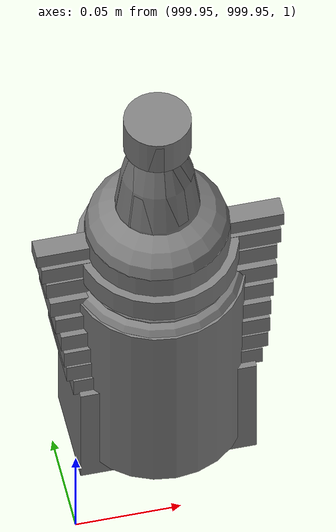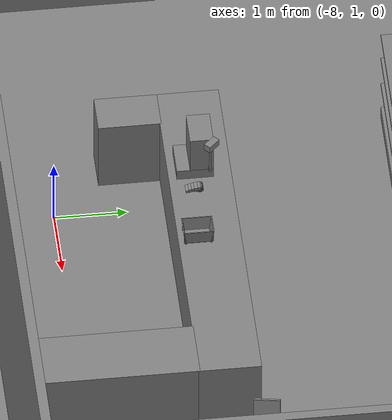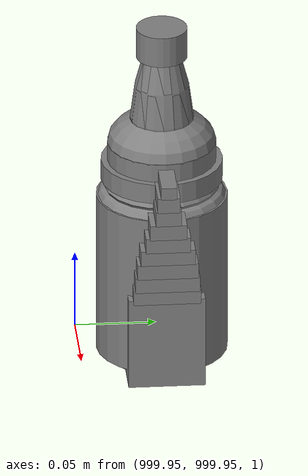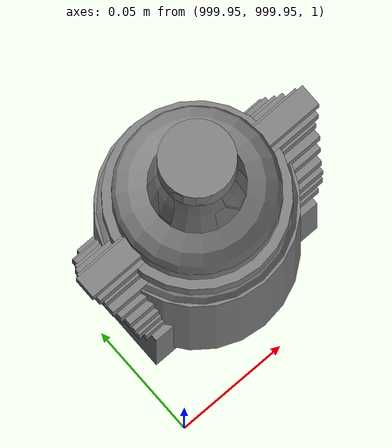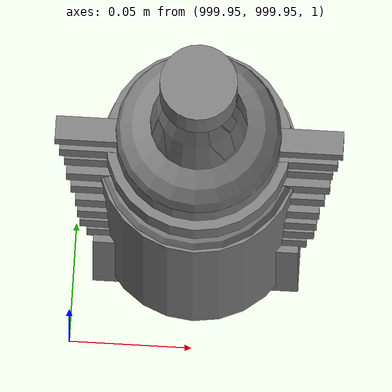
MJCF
<mujoco>
    <option gravity="0.000000000 0.000000000 -9.810000420" timestep="0.0166666" integrator="implicitfast" density="1.225" viscosity="1.8000001e-05" noslip_iterations="10" iterations="100" sdf_iterations="50">
        <flag multiccd="disable"/>
    </option>
    <size memory="1000M"/>
    <compiler coordinate="local"/>
    <worldbody>
        <light cutoff="30" pos="0 1 1" dir="0 -1 -2"/>
        <light cutoff="30" pos="0 -1 1" dir="0 1 -2"/>
        <body pos="0.000000000 0.000000000 0.000000000" euler="0.000000000 0.000000000 0.000000000" name="Interactive Objects_Interactive Objects"/>
        <body pos="-2.142765999 5.981794834 1.707017064" euler="128.226516724 -42.201644897 -54.500713348" mocap="true" name="spotlight2_SpotLight"/>
        <body pos="-2.234827995 6.087822914 1.848775387" euler="-129.414916992 61.361488342 -130.198348999" mocap="true" name="spotlight6_SpotLight"/>
        <body pos="1000.000000000 1000.000000000 1.000000000" euler="0.000000000 0.000000000 0.000000000" name="openloong_gripper_2f85_fix_base_usda_bottle_blue">
            <geom contype="1" conaffinity="1" density="1000" type="ellipsoid" material="" rgba="0.500000000 0.500000000 0.500000000 1.000000000" solimp="0.899999976 0.949999988 0.001000000" friction="1.000000000 0.005000000 0.000100000" solref="0.020000000 1.000000000" margin="0" condim="3" group="0" pos="0.000000000 0.000000000 0.118920922" quat="1.000000000 0.000000000 0.000000000 0.000000000" size="0.030999999 0.030999999 0.029999999" name="openloong_gripper_2f85_fix_base_usda_geom_77F7C211_660A_452F_8FFF_9C5F5C477827"/>
            <geom contype="1" conaffinity="1" density="1000" type="box" material="" rgba="0.500000000 0.500000000 0.500000000 1.000000000" solimp="0.899999976 0.949999988 0.001000000" friction="1.000000000 0.005000000 0.000100000" solref="0.020000000 1.000000000" margin="0" condim="3" group="0" pos="0.000000000 0.000000000 0.002164602" quat="1.000000000 0.000000000 0.000000000 0.000000000" size="0.020000000 0.020000000 0.003000000" name="openloong_gripper_2f85_fix_base_usda_geom_4399526E_2B2C_465B_9A16_CE39CF36DF1E"/>
            <geom contype="1" conaffinity="1" density="1000" type="cylinder" material="" rgba="0.500000000 0.500000000 0.500000000 1.000000000" solimp="0.899999976 0.949999988 0.001000000" friction="1.000000000 0.005000000 0.000100000" solref="0.020000000 1.000000000" margin="0" condim="3" group="0" pos="0.000000000 -0.000366211 0.060859680" quat="1.000000000 0.000000000 0.000000000 0.000000000" size="0.030999999 0.057999998 1.000000000" name="openloong_gripper_2f85_fix_base_usda_geom_D35A7CB8_F05F_439F_939E_CBABA1CD8FAC"/>
            <geom contype="1" conaffinity="1" density="1000" type="cylinder" material="" rgba="0.500000000 0.500000000 0.500000000 1.000000000" solimp="0.899999976 0.949999988 0.001000000" friction="1.000000000 0.005000000 0.000100000" solref="0.020000000 1.000000000" margin="0" condim="3" group="0" pos="0.000000000 0.000000000 0.220594406" quat="1.000000000 0.000000000 0.000000000 0.000000000" size="0.016000001 0.010000000 1.000000000" name="openloong_gripper_2f85_fix_base_usda_geom_A35E5852_497E_4240_8AF0_CB783EC3914B"/>
            <geom contype="1" conaffinity="1" density="1000" type="ellipsoid" material="" rgba="0.500000000 0.500000000 0.500000000 1.000000000" solimp="0.899999976 0.949999988 0.001000000" friction="1.000000000 0.005000000 0.000100000" solref="0.020000000 1.000000000" margin="0" condim="3" group="0" pos="0.000000000 0.000000000 0.144259930" quat="1.000000000 0.000000000 0.000000000 0.000000000" size="0.021000000 0.021000000 0.079999998" name="openloong_gripper_2f85_fix_base_usda_geom_C3D15B0E_EE56_40B6_B17F_E7457485D867"/>
            <freejoint name="openloong_gripper_2f85_fix_base_usda_bottle_blue_joint"/>
            <site size="0.005000000 0.005000000 0.005000000" rgba="0.500000000 0.500000000 0.500000000 1.000000000" pos="0.000000000 0.000000000 0.000000000" quat="0.999961913 0.008726535 0.000000000 0.000000000" group="0" type="sphere" name="openloong_gripper_2f85_fix_base_usda_bottle_bluesite"/>
        </body>
        <body pos="1000.000000000 1000.000000000 1.000000000" euler="0.000000000 0.000000000 0.000000000" name="openloong_gripper_2f85_fix_base_usda_can">
            <geom contype="1" conaffinity="1" density="1000" type="cylinder" material="" rgba="0.500000000 0.500000000 0.500000000 1.000000000" solimp="0.899999976 0.949999988 0.001000000" friction="1.000000000 0.005000000 0.000100000" solref="0.020000000 1.000000000" margin="0" condim="3" group="0" pos="0.000000000 0.000000000 0.079676986" quat="1.000000000 0.000000000 0.000000000 0.000000000" size="0.034000002 0.071999997 1.000000000" name="openloong_gripper_2f85_fix_base_usda_geom_D7A8C3A9_BCE8_459F_BE1E_57103F883F62"/>
            <geom contype="1" conaffinity="1" density="1000" type="ellipsoid" material="" rgba="0.500000000 0.500000000 0.500000000 1.000000000" solimp="0.899999976 0.949999988 0.001000000" friction="1.000000000 0.005000000 0.000100000" solref="0.020000000 1.000000000" margin="0" condim="3" group="0" pos="0.000000000 0.000000000 0.151854277" quat="1.000000000 0.000000000 0.000000000 0.000000000" size="0.034000002 0.034000002 0.020000000" name="openloong_gripper_2f85_fix_base_usda_geom_7E4B738C_E2D6_451B_A398_9B2D224C1D65"/>
            <geom contype="1" conaffinity="1" density="1000" type="box" material="" rgba="0.500000000 0.500000000 0.500000000 1.000000000" solimp="0.899999976 0.949999988 0.001000000" friction="1.000000000 0.005000000 0.000100000" solref="0.020000000 1.000000000" margin="0" condim="3" group="0" pos="0.000000000 0.000000000 0.004777670" quat="1.000000000 0.000000000 0.000000000 0.000000000" size="0.020000000 0.020000000 0.005000000" name="openloong_gripper_2f85_fix_base_usda_geom_1BBB2F7A_BF29_4177_916E_0C0B3A976D82"/>
            <freejoint name="openloong_gripper_2f85_fix_base_usda_can_joint"/>
            <site size="0.005000000 0.005000000 0.005000000" rgba="0.500000000 0.500000000 0.500000000 1.000000000" pos="0.000000000 0.000000000 0.000000000" quat="1.000000000 0.000000000 0.000000000 0.000000000" group="0" type="sphere" name="openloong_gripper_2f85_fix_base_usda_cansite"/>
        </body>
        <body pos="1000.000000000 1000.000000000 1.000000000" euler="0.000000000 0.000000000 0.000000000" name="openloong_gripper_2f85_fix_base_usda_salt">
            <geom contype="1" conaffinity="1" density="1000" type="box" material="" rgba="0.500000000 0.500000000 0.500000000 1.000000000" solimp="0.899999976 0.949999988 0.001000000" friction="1.000000000 0.005000000 0.000100000" solref="0.020000000 1.000000000" margin="0" condim="3" group="0" pos="0.000305176 0.000000000 0.084862232" quat="1.000000000 0.000000000 0.000000000 0.000000000" size="0.048999999 0.018999999 0.005000000" name="openloong_gripper_2f85_fix_base_usda_geom_579D315A_CDB5_48B0_ACEA_51449B813E32"/>
            <geom contype="1" conaffinity="1" density="1000" type="box" material="" rgba="0.500000000 0.500000000 0.500000000 1.000000000" solimp="0.899999976 0.949999988 0.001000000" friction="1.000000000 0.005000000 0.000100000" solref="0.020000000 1.000000000" margin="0" condim="3" group="0" pos="0.000305176 0.000000000 0.104564309" quat="1.000000000 0.000000000 0.000000000 0.000000000" size="0.052000001 0.014000000 0.005000000" name="openloong_gripper_2f85_fix_base_usda_geom_887DC398_15A9_4D57_B248_4B92027F6058"/>
            <geom contype="1" conaffinity="1" density="1000" type="box" material="" rgba="0.500000000 0.500000000 0.500000000 1.000000000" solimp="0.899999976 0.949999988 0.001000000" friction="1.000000000 0.005000000 0.000100000" solref="0.020000000 1.000000000" margin="0" condim="3" group="0" pos="0.000305176 0.000000000 0.114487171" quat="1.000000000 0.000000000 0.000000000 0.000000000" size="0.054000001 0.011500000 0.005000000" name="openloong_gripper_2f85_fix_base_usda_geom_7C6EB983_7003_443D_B20B_17D77BF04547"/>
            <geom contype="1" conaffinity="1" density="1000" type="box" material="" rgba="0.500000000 0.500000000 0.500000000 1.000000000" solimp="0.899999976 0.949999988 0.001000000" friction="1.000000000 0.005000000 0.000100000" solref="0.020000000 1.000000000" margin="0" condim="3" group="0" pos="0.000305176 0.000000000 0.075103164" quat="1.000000000 0.000000000 0.000000000 0.000000000" size="0.048000000 0.020000000 0.005000000" name="openloong_gripper_2f85_fix_base_usda_geom_682E1E8D_616A_469B_BB56_6CB8236704D0"/>
            <geom contype="1" conaffinity="1" density="1000" type="box" material="" rgba="0.500000000 0.500000000 0.500000000 1.000000000" solimp="0.899999976 0.949999988 0.001000000" friction="1.000000000 0.005000000 0.000100000" solref="0.020000000 1.000000000" margin="0" condim="3" group="0" pos="0.000305176 0.000000000 0.134892464" quat="1.000000000 0.000000000 0.000000000 0.000000000" size="0.057000000 0.007000000 0.005000000" name="openloong_gripper_2f85_fix_base_usda_geom_C0829555_C1D9_4022_A224_ECDE37E42918"/>
            <geom contype="1" conaffinity="1" density="1000" type="box" material="" rgba="0.500000000 0.500000000 0.500000000 1.000000000" solimp="0.899999976 0.949999988 0.001000000" friction="1.000000000 0.005000000 0.000100000" solref="0.020000000 1.000000000" margin="0" condim="3" group="0" pos="0.000305176 0.000000000 0.094920278" quat="1.000000000 0.000000000 0.000000000 0.000000000" size="0.050000001 0.017000001 0.005000000" name="openloong_gripper_2f85_fix_base_usda_geom_754DF073_E28E_4490_877F_F4377E1D130C"/>
            <geom contype="1" conaffinity="1" density="1000" type="box" material="" rgba="0.500000000 0.500000000 0.500000000 1.000000000" solimp="0.899999976 0.949999988 0.001000000" friction="1.000000000 0.005000000 0.000100000" solref="0.020000000 1.000000000" margin="0" condim="3" group="0" pos="0.000305176 0.000000000 0.065204859" quat="1.000000000 0.000000000 0.000000000 0.000000000" size="0.045000002 0.021000000 0.005000000" name="openloong_gripper_2f85_fix_base_usda_geom_2EB979FB_1227_4624_A63B_2C963904EEDC"/>
            <geom contype="1" conaffinity="1" density="1000" type="box" material="" rgba="0.500000000 0.500000000 0.500000000 1.000000000" solimp="0.899999976 0.949999988 0.001000000" friction="1.000000000 0.005000000 0.000100000" solref="0.020000000 1.000000000" margin="0" condim="3" group="0" pos="0.000305176 0.000000000 0.144135714" quat="1.000000000 0.000000000 0.000000000 0.000000000" size="0.059000000 0.005000000 0.004000000" name="openloong_gripper_2f85_fix_base_usda_geom_45864237_2C8C_4FFD_A746_FFBFE2EBDEE1"/>
            <geom contype="1" conaffinity="1" density="1000" type="box" material="" rgba="0.500000000 0.500000000 0.500000000 1.000000000" solimp="0.899999976 0.949999988 0.001000000" friction="1.000000000 0.005000000 0.000100000" solref="0.020000000 1.000000000" margin="0" condim="3" group="0" pos="0.000000000 0.000000000 0.031593561" quat="1.000000000 0.000000000 0.000000000 0.000000000" size="0.041999999 0.024000000 0.029999999" name="openloong_gripper_2f85_fix_base_usda_geom_C267C545_33FE_42A5_9623_004BD782DD95"/>
            <geom contype="1" conaffinity="1" density="1000" type="box" material="" rgba="0.500000000 0.500000000 0.500000000 1.000000000" solimp="0.899999976 0.949999988 0.001000000" friction="1.000000000 0.005000000 0.000100000" solref="0.020000000 1.000000000" margin="0" condim="3" group="0" pos="0.000305176 0.000000000 0.124608755" quat="1.000000000 0.000000000 0.000000000 0.000000000" size="0.055000000 0.008000000 0.005000000" name="openloong_gripper_2f85_fix_base_usda_geom_40D131BE_0948_490E_A5F3_58591E05BABD"/>
            <freejoint name="openloong_gripper_2f85_fix_base_usda_salt_joint"/>
            <site size="0.005000000 0.005000000 0.005000000" rgba="0.500000000 0.500000000 0.500000000 1.000000000" pos="0.000000000 0.000000000 0.000000000" quat="1.000000000 0.000000000 0.000000000 0.000000000" group="0" type="sphere" name="openloong_gripper_2f85_fix_base_usda_saltsite"/>
        </body>
        <body pos="-2.070525885 6.252047062 1.841474056" euler="6.906093121 -16.534505844 134.284667969" mocap="true" name="spotlight3_SpotLight"/>
        <body pos="1000.000000000 1000.000000000 1.000000000" euler="0.000000000 0.000000000 0.000000000" name="openloong_gripper_2f85_fix_base_usda_bottle_red">
            <geom contype="1" conaffinity="1" density="1000" type="ellipsoid" material="" rgba="0.500000000 0.500000000 0.500000000 1.000000000" solimp="0.899999976 0.949999988 0.001000000" friction="1.000000000 0.005000000 0.000100000" solref="0.020000000 1.000000000" margin="0" condim="3" group="0" pos="0.000000000 0.000000000 0.144284487" quat="1.000000000 0.000000000 0.000000000 0.000000000" size="0.021000000 0.021000000 0.079999998" name="openloong_gripper_2f85_fix_base_usda_geom_DD8D978B_0CA7_40ED_BC64_48A34EC7CB03"/>
            <geom contype="1" conaffinity="1" density="1000" type="cylinder" material="" rgba="0.500000000 0.500000000 0.500000000 1.000000000" solimp="0.899999976 0.949999988 0.001000000" friction="1.000000000 0.005000000 0.000100000" solref="0.020000000 1.000000000" margin="0" condim="3" group="0" pos="0.000000000 0.000000000 0.220618963" quat="1.000000000 0.000000000 0.000000000 0.000000000" size="0.016000001 0.010000000 1.000000000" name="openloong_gripper_2f85_fix_base_usda_geom_9084732A_9896_467A_B2BF_50520DFB69DE"/>
            <geom contype="1" conaffinity="1" density="1000" type="ellipsoid" material="" rgba="0.500000000 0.500000000 0.500000000 1.000000000" solimp="0.899999976 0.949999988 0.001000000" friction="1.000000000 0.005000000 0.000100000" solref="0.020000000 1.000000000" margin="0" condim="3" group="0" pos="0.000000000 0.000000000 0.118945479" quat="1.000000000 0.000000000 0.000000000 0.000000000" size="0.030999999 0.030999999 0.029999999" name="openloong_gripper_2f85_fix_base_usda_geom_2A405FE8_8655_4D0C_B7F0_5BF3D809CD64"/>
            <geom contype="1" conaffinity="1" density="1000" type="box" material="" rgba="0.500000000 0.500000000 0.500000000 1.000000000" solimp="0.899999976 0.949999988 0.001000000" friction="1.000000000 0.005000000 0.000100000" solref="0.020000000 1.000000000" margin="0" condim="3" group="0" pos="0.000000000 0.000000000 0.002189159" quat="1.000000000 0.000000000 0.000000000 0.000000000" size="0.020000000 0.020000000 0.003000000" name="openloong_gripper_2f85_fix_base_usda_geom_75C28D0A_3B9C_420C_A916_5B6EA964D25B"/>
            <geom contype="1" conaffinity="1" density="1000" type="cylinder" material="" rgba="0.500000000 0.500000000 0.500000000 1.000000000" solimp="0.899999976 0.949999988 0.001000000" friction="1.000000000 0.005000000 0.000100000" solref="0.020000000 1.000000000" margin="0" condim="3" group="0" pos="0.000000000 -0.000366211 0.060884237" quat="1.000000000 0.000000000 0.000000000 0.000000000" size="0.030999999 0.057999998 1.000000000" name="openloong_gripper_2f85_fix_base_usda_geom_76BCA771_3129_43D7_88E9_73A4A31DB9EB"/>
            <freejoint name="openloong_gripper_2f85_fix_base_usda_bottle_red_joint"/>
            <site size="0.005000000 0.005000000 0.005000000" rgba="0.500000000 0.500000000 0.500000000 1.000000000" pos="0.000000000 0.000000000 0.000000000" quat="0.999961913 0.008726535 0.000000000 0.000000000" group="0" type="sphere" name="openloong_gripper_2f85_fix_base_usda_bottle_redsite"/>
        </body>
        <body pos="1000.000000000 1000.000000000 1.000000000" euler="0.000000000 0.000000000 0.000000000" name="openloong_gripper_2f85_fix_base_usda_jar_01">
            <geom contype="1" conaffinity="1" density="1000" type="box" material="" rgba="0.500000000 0.500000000 0.500000000 1.000000000" solimp="0.899999976 0.949999988 0.001000000" friction="1.000000000 0.005000000 0.000100000" solref="0.020000000 1.000000000" margin="0" condim="3" group="0" pos="0.000000000 0.000000000 0.006158113" quat="1.000000000 0.000000000 0.000000000 0.000000000" size="0.020000000 0.020000000 0.005000000" name="openloong_gripper_2f85_fix_base_usda_geom_94248C07_3753_4664_B151_3D65B927F6E9"/>
            <geom contype="1" conaffinity="1" density="1000" type="cylinder" material="" rgba="0.500000000 0.500000000 0.500000000 1.000000000" solimp="0.899999976 0.949999988 0.001000000" friction="1.000000000 0.005000000 0.000100000" solref="0.020000000 1.000000000" margin="0" condim="3" group="0" pos="0.000000000 0.000000000 0.062744498" quat="1.000000000 0.000000000 0.000000000 0.000000000" size="0.041000001 0.052999999 1.000000000" name="openloong_gripper_2f85_fix_base_usda_geom_63B80697_B307_4847_876A_A803CC8983DF"/>
            <geom contype="1" conaffinity="1" density="1000" type="ellipsoid" material="" rgba="0.500000000 0.500000000 0.500000000 1.000000000" solimp="0.899999976 0.949999988 0.001000000" friction="1.000000000 0.005000000 0.000100000" solref="0.020000000 1.000000000" margin="0" condim="3" group="0" pos="0.000000000 0.000000000 0.122252703" quat="1.000000000 0.000000000 0.000000000 0.000000000" size="0.035999998 0.035999998 0.010000000" name="openloong_gripper_2f85_fix_base_usda_geom_436B00FF_6477_474E_A450_5720A07D8250"/>
            <geom contype="1" conaffinity="1" density="1000" type="cylinder" material="" rgba="0.500000000 0.500000000 0.500000000 1.000000000" solimp="0.899999976 0.949999988 0.001000000" friction="1.000000000 0.005000000 0.000100000" solref="0.020000000 1.000000000" margin="0" condim="3" group="0" pos="0.000000000 0.000000000 0.015747190" quat="1.000000000 0.000000000 0.000000000 0.000000000" size="0.035000000 0.010000000 1.000000000" name="openloong_gripper_2f85_fix_base_usda_geom_BB9CEDE7_3231_4540_95B9_08F4463C4040"/>
            <geom contype="1" conaffinity="1" density="1000" type="ellipsoid" material="" rgba="0.500000000 0.500000000 0.500000000 1.000000000" solimp="0.899999976 0.949999988 0.001000000" friction="1.000000000 0.005000000 0.000100000" solref="0.020000000 1.000000000" margin="0" condim="3" group="0" pos="0.000000000 0.000000000 0.115815401" quat="1.000000000 0.000000000 0.000000000 0.000000000" size="0.039999999 0.039999999 0.010000000" name="openloong_gripper_2f85_fix_base_usda_geom_6BEF6286_F9ED_43BF_9B8D_36D91642E16F"/>
            <geom contype="1" conaffinity="1" density="1000" type="cylinder" material="" rgba="0.500000000 0.500000000 0.500000000 1.000000000" solimp="0.899999976 0.949999988 0.001000000" friction="1.000000000 0.005000000 0.000100000" solref="0.020000000 1.000000000" margin="0" condim="3" group="0" pos="0.000000000 0.000000000 0.133183479" quat="1.000000000 0.000000000 0.000000000 0.000000000" size="0.037999999 0.006500000 1.000000000" name="openloong_gripper_2f85_fix_base_usda_geom_10138B8C_4DA4_46AD_AA30_29397E14FCE3"/>
            <freejoint name="openloong_gripper_2f85_fix_base_usda_jar_01_joint"/>
            <site size="0.005000000 0.005000000 0.005000000" rgba="0.500000000 0.500000000 0.500000000 1.000000000" pos="0.000000000 0.000000000 0.000000000" quat="1.000000000 0.000000000 0.000000000 0.000000000" group="0" type="sphere" name="openloong_gripper_2f85_fix_base_usda_jar_01site"/>
        </body>
        <body pos="0.000000000 0.000000000 0.000000000" euler="0.000000000 0.000000000 0.000000000" name=" Static Objects_ Static Objects">
            <geom contype="1" conaffinity="1" density="1000" type="box" material="" rgba="0.500000000 0.500000000 0.500000000 1.000000000" solimp="0.899999976 0.949999988 0.001000000" friction="1.000000000 0.005000000 0.000100000" solref="0.020000000 1.000000000" margin="0" condim="3" group="0" pos="-6.286010742 6.153595448 1.563861728" quat="0.707107067 0.000000000 0.000000000 0.707106471" size="0.529999971 3.134999990 0.025000000" name=" Static Objects_geom_0ADCC0C4_E16B_42A7_AD34_16975CA5B757"/>
            <geom contype="1" conaffinity="1" density="1000" type="box" material="" rgba="0.500000000 0.500000000 0.500000000 1.000000000" solimp="0.899999976 0.949999988 0.001000000" friction="1.000000000 0.005000000 0.000100000" solref="0.020000000 1.000000000" margin="0" condim="3" group="0" pos="-3.101639986 6.150595188 1.018643856" quat="1.000000000 0.000000000 0.000000000 0.000000000" size="0.050000001 0.579999983 1.019999981" name=" Static Objects_geom_393A2F9D_70DD_4E12_8AC2_43AA53AAF275"/>
            <geom contype="1" conaffinity="1" density="1000" type="box" material="" rgba="0.500000000 0.500000000 0.500000000 1.000000000" solimp="0.899999976 0.949999988 0.001000000" friction="1.000000000 0.005000000 0.000100000" solref="0.020000000 1.000000000" margin="0" condim="3" group="0" pos="-2.825197220 6.153595448 1.563861728" quat="0.707107067 0.000000000 0.000000000 0.707106471" size="0.550000012 0.239999995 0.025000000" name=" Static Objects_geom_062A4BBA_DEFB_4F9D_BA4E_DB0B5B72EC68"/>
            <geom contype="1" conaffinity="1" density="1000" type="box" material="" rgba="0.500000000 0.500000000 0.500000000 1.000000000" solimp="0.899999976 0.949999988 0.001000000" friction="1.000000000 0.005000000 0.000100000" solref="0.020000000 1.000000000" margin="0" condim="3" group="0" pos="-6.311686516 6.153595448 1.018643856" quat="0.707107067 0.000000000 0.000000000 0.707106471" size="0.050000001 3.150000095 1.019999981" name=" Static Objects_geom_595DFFC0_F473_4338_91B6_F46FA2D90BD6"/>
            <geom contype="1" conaffinity="1" density="1000" type="box" material="" rgba="0.500000000 0.500000000 0.500000000 1.000000000" solimp="0.899999976 0.949999988 0.001000000" friction="1.000000000 0.005000000 0.000100000" solref="0.020000000 1.000000000" margin="0" condim="3" group="0" pos="-2.825197220 6.153595448 1.115278244" quat="0.707107067 0.000000000 0.000000000 0.707106471" size="0.550000012 0.239999995 0.025000000" name=" Static Objects_geom_34BC1F9F_912E_4E87_AC58_D48D21392ADA"/>
            <geom contype="1" conaffinity="1" density="1000" type="box" material="" rgba="0.500000000 0.500000000 0.500000000 1.000000000" solimp="0.899999976 0.949999988 0.001000000" friction="1.000000000 0.005000000 0.000100000" solref="0.020000000 1.000000000" margin="0" condim="3" group="0" pos="-6.293097973 6.153595448 1.114443064" quat="0.707107067 0.000000000 0.000000000 0.707106471" size="0.529999971 3.134999990 0.025000000" name=" Static Objects_geom_BBBF8107_39E3_48C1_A288_307D13568FE3"/>
            <geom contype="1" conaffinity="1" density="1000" type="box" material="" rgba="0.500000000 0.500000000 0.500000000 1.000000000" solimp="0.899999976 0.949999988 0.001000000" friction="1.000000000 0.005000000 0.000100000" solref="0.020000000 1.000000000" margin="0" condim="3" group="0" pos="-2.825197220 6.153595448 0.629031777" quat="0.707107067 0.000000000 0.000000000 0.707106471" size="0.550000012 0.239999995 0.025000000" name=" Static Objects_geom_476D92E6_073A_47AC_A65E_0B48ED36671D"/>
            <geom contype="1" conaffinity="1" density="1000" type="box" material="" rgba="0.500000000 0.500000000 0.500000000 1.000000000" solimp="0.899999976 0.949999988 0.001000000" friction="1.000000000 0.005000000 0.000100000" solref="0.020000000 1.000000000" margin="0" condim="3" group="0" pos="-6.286010742 6.153595448 0.096129179" quat="0.707107067 0.000000000 0.000000000 0.707106471" size="0.529999971 3.134999990 0.098999999" name=" Static Objects_geom_89C407F3_C56E_43D8_9D99_85AF0BA42DF1"/>
            <geom contype="1" conaffinity="1" density="1000" type="box" material="" rgba="0.500000000 0.500000000 0.500000000 1.000000000" solimp="0.899999976 0.949999988 0.001000000" friction="1.000000000 0.005000000 0.000100000" solref="0.020000000 1.000000000" margin="0" condim="3" group="0" pos="-2.825197220 6.153595448 0.097434282" quat="0.707107067 0.000000000 0.000000000 0.707106471" size="0.550000012 0.239999995 0.098999999" name=" Static Objects_geom_F4C6FC6D_6A7E_4DFF_B980_EF91336026C8"/>
            <geom contype="1" conaffinity="1" density="1000" type="box" material="" rgba="0.500000000 0.500000000 0.500000000 1.000000000" solimp="0.899999976 0.949999988 0.001000000" friction="1.000000000 0.005000000 0.000100000" solref="0.020000000 1.000000000" margin="0" condim="3" group="0" pos="-6.286010742 6.153595448 0.629031777" quat="0.707107067 0.000000000 0.000000000 0.707106471" size="0.529999971 3.134999990 0.025000000" name=" Static Objects_geom_52EB841E_0FFA_435C_BD8A_14FC50E17706"/>
            <geom contype="1" conaffinity="1" density="1000" type="box" material="" rgba="0.500000000 0.500000000 0.500000000 1.000000000" solimp="0.899999976 0.949999988 0.001000000" friction="1.000000000 0.005000000 0.000100000" solref="0.020000000 1.000000000" margin="0" condim="3" group="0" pos="-6.000000000 20.159999847 2.000000000" quat="1.000000000 0.000000000 0.000000000 0.000000000" size="6.079999924 0.070000000 2.000000000" name=" Static Objects_geom_0DBCA712_2249_4AF5_964C_E895013255B8"/>
            <geom contype="1" conaffinity="1" density="1000" type="box" material="" rgba="0.500000000 0.500000000 0.500000000 1.000000000" solimp="0.899999976 0.949999988 0.001000000" friction="1.000000000 0.005000000 0.000100000" solref="0.020000000 1.000000000" margin="0" condim="3" group="0" pos="-6.000000000 0.035000000 2.000000000" quat="1.000000000 0.000000000 0.000000000 0.000000000" size="6.079999924 0.070000000 2.000000000" name=" Static Objects_geom_5CC303CC_ECC5_4C9F_BD40_4801C63267BB"/>
            <geom contype="1" conaffinity="1" density="1000" type="box" material="" rgba="0.500000000 0.500000000 0.500000000 1.000000000" solimp="0.899999976 0.949999988 0.001000000" friction="1.000000000 0.005000000 0.000100000" solref="0.020000000 1.000000000" margin="0" condim="3" group="0" pos="0.000000000 10.000000000 2.000000000" quat="1.000000000 0.000000000 0.000000000 0.000000000" size="0.070000000 10.500000000 2.000000000" name=" Static Objects_geom_F6A6025A_3B8D_4198_A9F1_E04844245206"/>
            <geom contype="1" conaffinity="1" density="1000" type="box" material="" rgba="0.500000000 0.500000000 0.500000000 1.000000000" solimp="0.899999976 0.949999988 0.001000000" friction="1.000000000 0.005000000 0.000100000" solref="0.020000000 1.000000000" margin="0" condim="3" group="0" pos="-12.050000191 10.000000000 2.000000000" quat="1.000000000 0.000000000 0.000000000 0.000000000" size="0.070000000 10.500000000 2.000000000" name=" Static Objects_geom_FC909E8E_DD62_4292_BA43_D95CAA381C97"/>
            <geom contype="1" conaffinity="1" density="1000" type="plane" material="" rgba="0.500000000 0.500000000 0.500000000 1.000000000" solimp="0.899999976 0.949999988 0.001000000" friction="1.000000000 0.005000000 0.000100000" solref="0.020000000 1.000000000" margin="0" condim="3" group="0" pos="-6.000000000 10.399999619 0.000000000" quat="1.000000000 0.000000000 0.000000000 0.000000000" size="6.050000191 10.800000191 0.010000000" name=" Static Objects_geom_1E87AA0F_C1FF_47EE_80BC_6EDEA047FFBA"/>
            <geom contype="1" conaffinity="1" density="1000" type="box" material="" rgba="0.500000000 0.500000000 0.500000000 1.000000000" solimp="0.899999976 0.949999988 0.001000000" friction="1.000000000 0.005000000 0.000100000" solref="0.020000000 1.000000000" margin="0" condim="3" group="0" pos="-8.830721855 2.096410990 0.549305558" quat="1.000000000 0.000000000 0.000000000 0.000000000" size="0.280000001 0.430000007 0.550000012" name=" Static Objects_geom_9E37C1A6_E503_4775_BA7A_855A89C63A19"/>
            <geom contype="1" conaffinity="1" density="1000" type="box" material="" rgba="0.500000000 0.500000000 0.500000000 1.000000000" solimp="0.899999976 0.949999988 0.001000000" friction="1.000000000 0.005000000 0.000100000" solref="0.020000000 1.000000000" margin="0" condim="3" group="0" pos="-6.460197449 2.937205315 0.548931718" quat="1.000000000 0.000000000 0.000000000 0.000000000" size="2.650000095 0.430000007 0.550000012" name=" Static Objects_geom_E51C85E4_1800_4698_B1B9_DBDFDA872BF4"/>
            <geom contype="1" conaffinity="1" density="1000" type="box" material="" rgba="0.500000000 0.500000000 0.500000000 1.000000000" solimp="0.899999976 0.949999988 0.001000000" friction="1.000000000 0.005000000 0.000100000" solref="0.020000000 1.000000000" margin="0" condim="3" group="0" pos="-4.240264893 1.327049494 0.549888909" quat="1.000000000 0.000000000 0.000000000 0.000000000" size="0.430000007 1.200000048 0.550000012" name=" Static Objects_geom_04E858B9_6DB3_4CAE_82D6_971ACE227D85"/>
            <geom contype="1" conaffinity="1" density="1000" type="box" material="" rgba="0.500000000 0.500000000 0.500000000 1.000000000" solimp="0.899999976 0.949999988 0.001000000" friction="1.000000000 0.005000000 0.000100000" solref="0.020000000 1.000000000" margin="0" condim="3" group="0" pos="-7.408766270 3.088089943 1.776644945" quat="0.928051054 0.000000000 0.000000000 0.372453064" size="0.050000001 0.100000001 0.050000001" name=" Static Objects_geom_AF4FB93C_AAE1_4754_901C_CB1C403364E8"/>
            <geom contype="1" conaffinity="1" density="1000" type="box" material="" rgba="0.500000000 0.500000000 0.500000000 1.000000000" solimp="0.899999976 0.949999988 0.001000000" friction="1.000000000 0.005000000 0.000100000" solref="0.020000000 1.000000000" margin="0" condim="3" group="0" pos="-7.437745571 3.067511320 1.289965630" quat="1.000000000 0.000000000 0.000000000 0.000000000" size="0.029999999 0.020000000 0.020000000" name=" Static Objects_geom_70804947_6674_4286_A594_9FE60C2498DA"/>
            <geom contype="1" conaffinity="1" density="1000" type="box" material="" rgba="0.500000000 0.500000000 0.500000000 1.000000000" solimp="0.899999976 0.949999988 0.001000000" friction="1.000000000 0.005000000 0.000100000" solref="0.020000000 1.000000000" margin="0" condim="3" group="0" pos="-7.719123363 2.867671013 1.173410416" quat="1.000000000 0.000000000 0.000000000 0.000000000" size="0.250000000 0.250000000 0.079999998" name=" Static Objects_geom_1673CB5A_E21F_4577_A486_8A866EDCDC13"/>
            <geom contype="1" conaffinity="1" density="1000" type="box" material="" rgba="0.500000000 0.500000000 0.500000000 1.000000000" solimp="0.899999976 0.949999988 0.001000000" friction="1.000000000 0.005000000 0.000100000" solref="0.020000000 1.000000000" margin="0" condim="3" group="0" pos="-7.719123363 2.958004713 1.530241251" quat="1.000000000 0.000000000 0.000000000 0.000000000" size="0.250000000 0.159999996 0.280000001" name=" Static Objects_geom_F7F2F462_2884_415A_89D0_BF9FE830EFFA"/>
            <geom contype="1" conaffinity="1" density="1000" type="cylinder" material="" rgba="0.500000000 0.500000000 0.500000000 1.000000000" solimp="0.899999976 0.949999988 0.001000000" friction="1.000000000 0.005000000 0.000100000" solref="0.020000000 1.000000000" margin="0" condim="3" group="0" pos="-7.427312374 3.069516420 1.502544641" quat="0.928051054 0.000000000 0.000000000 0.372453064" size="0.015000000 0.230000004 0.100000001" name=" Static Objects_geom_1915D1DD_C09F_482F_A8BA_CF5ABB217180"/>
            <geom contype="1" conaffinity="1" density="1000" type="box" material="" rgba="0.500000000 0.500000000 0.500000000 1.000000000" solimp="0.899999976 0.949999988 0.001000000" friction="1.000000000 0.005000000 0.000100000" solref="0.020000000 1.000000000" margin="0" condim="3" group="0" pos="-9.058088303 6.434794426 1.209077358" quat="1.000000000 0.000000000 0.000000000 0.000000000" size="0.250000000 0.100000001 0.070000000" name=" Static Objects_geom_BAB66F5A_E469_4C31_B6A1_00E516A1BF3E"/>
            <geom contype="1" conaffinity="1" density="1000" type="box" material="" rgba="0.500000000 0.500000000 0.500000000 1.000000000" solimp="0.899999976 0.949999988 0.001000000" friction="1.000000000 0.005000000 0.000100000" solref="0.020000000 1.000000000" margin="0" condim="3" group="0" pos="-5.611940861 6.318420410 0.350975692" quat="1.000000000 0.000000000 0.000000000 0.000000000" size="0.699999988 0.100000001 0.150000006" name=" Static Objects_geom_976A9AB5_EA88_46C2_838E_7B108F3ADA5E"/>
            <geom contype="1" conaffinity="1" density="1000" type="box" material="" rgba="0.500000000 0.500000000 0.500000000 1.000000000" solimp="0.899999976 0.949999988 0.001000000" friction="1.000000000 0.005000000 0.000100000" solref="0.020000000 1.000000000" margin="0" condim="3" group="0" pos="-9.237723351 6.464855671 1.209077358" quat="1.000000000 0.000000000 0.000000000 0.000000000" size="0.100000001 0.100000001 0.070000000" name=" Static Objects_geom_AFD1E9FB_F4D7_4842_8705_624E557BF65F"/>
            <geom contype="1" conaffinity="1" density="1000" type="box" material="" rgba="0.500000000 0.500000000 0.500000000 1.000000000" solimp="0.899999976 0.949999988 0.001000000" friction="1.000000000 0.005000000 0.000100000" solref="0.020000000 1.000000000" margin="0" condim="3" group="0" pos="-6.300771236 6.459744930 1.744376063" quat="1.000000000 0.000000000 0.000000000 0.000000000" size="3.000000000 0.200000003 0.150000006" name=" Static Objects_geom_BA29B71F_1CE4_49CF_8E37_3BF43E598632"/>
            <geom contype="1" conaffinity="1" density="1000" type="box" material="" rgba="0.500000000 0.500000000 0.500000000 1.000000000" solimp="0.899999976 0.949999988 0.001000000" friction="1.000000000 0.005000000 0.000100000" solref="0.020000000 1.000000000" margin="0" condim="3" group="0" pos="-7.373087406 6.458900928 1.214329123" quat="1.000000000 0.000000000 0.000000000 0.000000000" size="0.250000000 0.200000003 0.075000003" name=" Static Objects_geom_5367F08D_72E3_4C66_A817_964F7377B08A"/>
            <geom contype="1" conaffinity="1" density="1000" type="box" material="" rgba="0.500000000 0.500000000 0.500000000 1.000000000" solimp="0.899999976 0.949999988 0.001000000" friction="1.000000000 0.005000000 0.000100000" solref="0.020000000 1.000000000" margin="0" condim="3" group="0" pos="-4.035642624 6.459744930 0.352518857" quat="1.000000000 0.000000000 0.000000000 0.000000000" size="0.800000012 0.200000003 0.150000006" name=" Static Objects_geom_3CE63A4B_1990_42F2_836A_C0F17044BB4C"/>
            <geom contype="1" conaffinity="1" density="1000" type="box" material="" rgba="0.500000000 0.500000000 0.500000000 1.000000000" solimp="0.899999976 0.949999988 0.001000000" friction="1.000000000 0.005000000 0.000100000" solref="0.020000000 1.000000000" margin="0" condim="3" group="0" pos="-3.907610416 6.318625927 0.800981164" quat="1.000000000 0.000000000 0.000000000 0.000000000" size="0.500000000 0.100000001 0.150000006" name=" Static Objects_geom_8FEAAE8C_39C7_410E_8BFC_5C8065FC4842"/>
            <geom contype="1" conaffinity="1" density="1000" type="box" material="" rgba="0.500000000 0.500000000 0.500000000 1.000000000" solimp="0.899999976 0.949999988 0.001000000" friction="1.000000000 0.005000000 0.000100000" solref="0.020000000 1.000000000" margin="0" condim="3" group="0" pos="-6.098561764 6.327973843 1.292199373" quat="1.000000000 0.000000000 0.000000000 0.000000000" size="0.500000000 0.100000001 0.150000006" name=" Static Objects_geom_10E77B3E_DB0C_4C4A_B871_DBD5B71F44AA"/>
            <geom contype="1" conaffinity="1" density="1000" type="box" material="" rgba="0.500000000 0.500000000 0.500000000 1.000000000" solimp="0.899999976 0.949999988 0.001000000" friction="1.000000000 0.005000000 0.000100000" solref="0.020000000 1.000000000" margin="0" condim="3" group="0" pos="-7.886891365 6.459744930 0.352518857" quat="1.000000000 0.000000000 0.000000000 0.000000000" size="1.500000000 0.200000003 0.150000006" name=" Static Objects_geom_8858AC0A_9827_4EAA_94B1_B2CB3A675CA9"/>
            <geom contype="1" conaffinity="1" density="1000" type="box" material="" rgba="0.500000000 0.500000000 0.500000000 1.000000000" solimp="0.899999976 0.949999988 0.001000000" friction="1.000000000 0.005000000 0.000100000" solref="0.020000000 1.000000000" margin="0" condim="3" group="0" pos="-6.824534416 6.447464466 1.212718010" quat="1.000000000 0.000000000 0.000000000 0.000000000" size="0.100000001 0.100000001 0.075000003" name=" Static Objects_geom_0BF981AE_4E49_4FB8_BE4F_DA6E54EB1DB3"/>
            <geom contype="1" conaffinity="1" density="1000" type="box" material="" rgba="0.500000000 0.500000000 0.500000000 1.000000000" solimp="0.899999976 0.949999988 0.001000000" friction="1.000000000 0.005000000 0.000100000" solref="0.020000000 1.000000000" margin="0" condim="3" group="0" pos="-4.407354832 6.459744930 1.292199373" quat="1.000000000 0.000000000 0.000000000 0.000000000" size="1.240000010 0.200000003 0.150000006" name=" Static Objects_geom_E25BC09B_BBB8_49C3_B312_DF0B37E833AF"/>
            <geom contype="1" conaffinity="1" density="1000" type="box" material="" rgba="0.500000000 0.500000000 0.500000000 1.000000000" solimp="0.899999976 0.949999988 0.001000000" friction="1.000000000 0.005000000 0.000100000" solref="0.020000000 1.000000000" margin="0" condim="3" group="0" pos="-6.751636982 6.459744930 0.800981164" quat="1.000000000 0.000000000 0.000000000 0.000000000" size="2.200000048 0.200000003 0.150000006" name=" Static Objects_geom_A44DCB98_E61D_42D1_AF3B_21FD34F1E98B"/>
            <geom contype="1" conaffinity="1" density="1000" type="box" material="" rgba="0.500000000 0.500000000 0.500000000 1.000000000" solimp="0.899999976 0.949999988 0.001000000" friction="1.000000000 0.005000000 0.000100000" solref="0.020000000 1.000000000" margin="0" condim="3" group="0" pos="-6.924745083 6.362090111 1.214329123" quat="1.000000000 0.000000000 0.000000000 0.000000000" size="0.200000003 0.100000001 0.075000003" name=" Static Objects_geom_8E553F7C_4876_4A67_9F74_4FE5F4A704DD"/>
            <geom contype="1" conaffinity="1" density="1000" type="box" material="" rgba="0.500000000 0.500000000 0.500000000 1.000000000" solimp="0.899999976 0.949999988 0.001000000" friction="1.000000000 0.005000000 0.000100000" solref="0.020000000 1.000000000" margin="0" condim="3" group="0" pos="-8.844120979 6.464855671 1.209077358" quat="1.000000000 0.000000000 0.000000000 0.000000000" size="0.100000001 0.100000001 0.070000000" name=" Static Objects_geom_2043BCB7_A1CE_4005_8CBD_466A4B41690E"/>
            <geom contype="1" conaffinity="1" density="1000" type="box" material="" rgba="0.500000000 0.500000000 0.500000000 1.000000000" solimp="0.899999976 0.949999988 0.001000000" friction="1.000000000 0.005000000 0.000100000" solref="0.020000000 1.000000000" margin="0" condim="3" group="0" pos="-3.157672644 6.136868477 1.348373055" quat="1.000000000 0.000000000 0.000000000 0.000000000" size="0.200000003 0.519999981 0.300000012" name=" Static Objects_geom_7B97C0F7_24D4_440D_88FD_C82D33AF82A1"/>
        </body>
        <body pos="-6.332345009 2.779978037 1.034067392" euler="0.000000000 0.000000000 0.000000000" name="openloong_gripper_2f85_fix_base_usda_basket">
            <geom contype="1" conaffinity="1" density="100000" type="box" material="" rgba="0.500000000 0.500000000 0.500000000 1.000000000" solimp="0.899999976 0.949999988 0.001000000" friction="1.000000000 0.899999976 0.000100000" solref="0.020000000 1.000000000" margin="0" condim="3" group="0" pos="-0.039724827 -0.188568115 0.167089701" quat="0.997537494 0.070135131 0.000000000 0.000000000" size="0.150000006 0.006000000 0.108000003" name="openloong_gripper_2f85_fix_base_usda_geom_ECA85B9A_4891_4C87_9682_E0B3570394B4"/>
            <geom contype="1" conaffinity="1" density="100000" type="box" material="" rgba="0.500000000 0.500000000 0.500000000 1.000000000" solimp="0.899999976 0.949999988 0.001000000" friction="1.000000000 0.899999976 0.000100000" solref="0.020000000 1.000000000" margin="0" condim="3" group="0" pos="0.094372749 0.000000000 0.168361664" quat="0.706172049 0.036353335 0.036353379 0.706171215" size="0.200000003 0.006000000 0.108000003" name="openloong_gripper_2f85_fix_base_usda_geom_7BB7E240_92E2_4C96_9EB5_A82E200333DF"/>
            <geom contype="1" conaffinity="1" density="100000" type="box" material="" rgba="0.500000000 0.500000000 0.500000000 1.000000000" solimp="0.899999976 0.949999988 0.001000000" friction="1.000000000 0.899999976 0.000100000" solref="0.020000000 1.000000000" margin="0" condim="3" group="0" pos="-0.039724827 0.000000000 0.068126202" quat="1.000000000 0.000000000 0.000000000 0.000000000" size="0.129999995 0.174999997 0.006000000" name="openloong_gripper_2f85_fix_base_usda_geom_796BFDE4_1D51_472F_B824_349392967380"/>
            <geom contype="1" conaffinity="1" density="100000" type="box" material="" rgba="0.500000000 0.500000000 0.500000000 1.000000000" solimp="0.899999976 0.949999988 0.001000000" friction="1.000000000 0.899999976 0.000100000" solref="0.020000000 1.000000000" margin="0" condim="3" group="0" pos="-0.039724827 0.188377380 0.167089701" quat="0.997489929 -0.070808925 0.000000000 0.000000000" size="0.150000006 0.006000000 0.108000003" name="openloong_gripper_2f85_fix_base_usda_geom_6F345842_9704_4C8A_88DF_1215C9C97974"/>
            <geom contype="1" conaffinity="1" density="100000" type="box" material="" rgba="0.500000000 0.500000000 0.500000000 1.000000000" solimp="0.899999976 0.949999988 0.001000000" friction="1.000000000 0.899999976 0.000100000" solref="0.020000000 1.000000000" margin="0" condim="3" group="0" pos="-0.172339439 0.000000000 0.168361664" quat="0.706172407 -0.036353018 -0.036353093 0.706170976" size="0.200000003 0.006000000 0.108000003" name="openloong_gripper_2f85_fix_base_usda_geom_AD97C3F1_BF09_4798_8295_26F3A7D697F4"/>
            <freejoint name="openloong_gripper_2f85_fix_base_usda_basket_joint"/>
            <site size="0.005000000 0.005000000 0.005000000" rgba="0.500000000 0.500000000 0.500000000 1.000000000" pos="0.000000000 0.000000000 0.000000000" quat="1.000000000 0.000000000 0.000000000 0.000000000" group="0" type="sphere" name="openloong_gripper_2f85_fix_base_usda_basketsite"/>
        </body>
        <body pos="-3.510578632 3.403555870 -0.000000100" euler="0.000000000 0.000000000 40.200675964" name="openloong_gripper_2f85_fix_base_usda_PZ">
            <geom contype="1" conaffinity="1" density="1000" type="box" material="" rgba="0.500000000 0.500000000 0.500000000 1.000000000" solimp="0.899999976 0.949999988 0.001000000" friction="1.000000000 0.005000000 0.000100000" solref="0.020000000 1.000000000" margin="0" condim="3" group="0" pos="-0.047453165 0.056484699 0.373715430" quat="0.934750080 0.077914521 0.028795123 0.345459938" size="0.180000007 0.010000000 0.379999995" name="openloong_gripper_2f85_fix_base_usda_geom_8A27537E_4F0F_4B98_A83B_D6235281074B"/>
            <geom contype="1" conaffinity="1" density="1000" type="box" material="" rgba="0.500000000 0.500000000 0.500000000 1.000000000" solimp="0.899999976 0.949999988 0.001000000" friction="1.000000000 0.005000000 0.000100000" solref="0.020000000 1.000000000" margin="0" condim="3" group="0" pos="0.047452450 -0.054376602 0.374072611" quat="0.934387863 -0.082143910 -0.030358355 0.345326364" size="0.180000007 0.010000000 0.379999995" name="openloong_gripper_2f85_fix_base_usda_geom_D7660235_2FB3_4588_AB70_5289BF7AFFEB"/>
            <freejoint name="openloong_gripper_2f85_fix_base_usda_PZ"/>
        </body>
        <body pos="-7.168000221 2.823999882 1.227496982" euler="-0.283413976 0.056829724 -0.133293271" name="openloong_gripper_2f85_fix_base_usda_Pos">
            <geom contype="1" conaffinity="1" density="1000" type="box" material="" rgba="0.500000000 0.500000000 0.500000000 1.000000000" solimp="0.899999976 0.949999988 0.001000000" friction="1.000000000 0.005000000 0.000100000" solref="0.020000000 1.000000000" margin="0" condim="3" group="0" pos="-0.002278805 0.074524641 -0.004134059" quat="0.315989345 0.948763072 -0.000000000 0.000000000" size="0.059999999 0.013000000 0.035000000" name="openloong_gripper_2f85_fix_base_usda_geom_41B2056D_8016_4B58_A915_B346DDBE399D"/>
            <geom contype="1" conaffinity="1" density="1000" type="box" material="" rgba="0.500000000 0.500000000 0.500000000 1.000000000" solimp="0.899999976 0.949999988 0.001000000" friction="1.000000000 0.005000000 0.000100000" solref="0.020000000 1.000000000" margin="0" condim="3" group="0" pos="-0.002278805 0.078031301 0.008128285" quat="0.990447521 -0.137893379 -0.000000000 -0.000000000" size="0.059999999 0.010000000 0.035000000" name="openloong_gripper_2f85_fix_base_usda_geom_F28FA686_F362_4B59_9A90_C553A0BDD27A"/>
            <geom contype="1" conaffinity="1" density="1000" type="box" material="" rgba="0.500000000 0.500000000 0.500000000 1.000000000" solimp="0.899999976 0.949999988 0.001000000" friction="1.000000000 0.005000000 0.000100000" solref="0.020000000 1.000000000" margin="0" condim="3" group="0" pos="-0.002278805 0.080785275 -0.002596974" quat="0.287325472 -0.957833409 0.000000000 -0.000000000" size="0.059999999 0.013000000 0.035000000" name="openloong_gripper_2f85_fix_base_usda_geom_C31BAFEA_0C5A_4853_8E43_BBAC3A468A28"/>
            <geom contype="1" conaffinity="1" density="1000" type="box" material="" rgba="0.500000000 0.500000000 0.500000000 1.000000000" solimp="0.899999976 0.949999988 0.001000000" friction="1.000000000 0.005000000 0.000100000" solref="0.020000000 1.000000000" margin="0" condim="3" group="0" pos="-0.002278805 -0.098804474 -0.020146966" quat="0.988851666 0.148906454 0.000000000 -0.000000000" size="0.059999999 0.022000000 0.020000000" name="openloong_gripper_2f85_fix_base_usda_geom_8FB2A6F9_0D0D_471F_987B_90BB2A1C6B31"/>
            <geom contype="1" conaffinity="1" density="1000" type="box" material="" rgba="0.500000000 0.500000000 0.500000000 1.000000000" solimp="0.899999976 0.949999988 0.001000000" friction="1.000000000 0.005000000 0.000100000" solref="0.020000000 1.000000000" margin="0" condim="3" group="0" pos="-0.002279282 0.019920111 0.012102962" quat="0.995421767 0.095583342 -0.000000000 -0.000000000" size="0.059999999 0.025000000 0.026000001" name="openloong_gripper_2f85_fix_base_usda_geom_83908617_2563_47CE_BEAF_F4F3EEA87645"/>
            <geom contype="1" conaffinity="1" density="1000" type="box" material="" rgba="0.500000000 0.500000000 0.500000000 1.000000000" solimp="0.899999976 0.949999988 0.001000000" friction="1.000000000 0.005000000 0.000100000" solref="0.020000000 1.000000000" margin="0" condim="3" group="0" pos="-0.002279282 0.005734444 -0.014276862" quat="0.999571741 -0.029275302 -0.000000000 -0.000000000" size="0.059999999 0.050000001 0.010000000" name="openloong_gripper_2f85_fix_base_usda_geom_C5EFDEA3_F5F6_4270_830C_E0C3BA8489FF"/>
            <geom contype="1" conaffinity="1" density="1000" type="box" material="" rgba="0.500000000 0.500000000 0.500000000 1.000000000" solimp="0.899999976 0.949999988 0.001000000" friction="1.000000000 0.005000000 0.000100000" solref="0.020000000 1.000000000" margin="0" condim="3" group="0" pos="-0.002278805 0.079460382 0.007771969" quat="0.922590554 -0.385781586 0.000000000 -0.000000000" size="0.059999999 0.010000000 0.035000000" name="openloong_gripper_2f85_fix_base_usda_geom_AE2E71C8_1CD2_4542_9F49_7A72E79897C6"/>
            <geom contype="1" conaffinity="1" density="1000" type="box" material="" rgba="0.500000000 0.500000000 0.500000000 1.000000000" solimp="0.899999976 0.949999988 0.001000000" friction="1.000000000 0.005000000 0.000100000" solref="0.020000000 1.000000000" margin="0" condim="3" group="0" pos="-0.002279282 0.081384182 -0.001320124" quat="0.590483785 -0.807049930 0.000000000 -0.000000000" size="0.059999999 0.013000000 0.035000000" name="openloong_gripper_2f85_fix_base_usda_geom_07B40BD9_9735_4131_868D_9CA4BDA09FFB"/>
            <geom contype="1" conaffinity="1" density="1000" type="box" material="" rgba="0.500000000 0.500000000 0.500000000 1.000000000" solimp="0.899999976 0.949999988 0.001000000" friction="1.000000000 0.005000000 0.000100000" solref="0.020000000 1.000000000" margin="0" condim="3" group="0" pos="-0.002278805 -0.059297800 -0.007972836" quat="0.988851666 0.148906454 0.000000000 -0.000000000" size="0.059999999 0.020000000 0.022000000" name="openloong_gripper_2f85_fix_base_usda_geom_B217CFF2_0262_4980_A7B8_98B7CE9875F6"/>
            <geom contype="1" conaffinity="1" density="1000" type="box" material="" rgba="0.500000000 0.500000000 0.500000000 1.000000000" solimp="0.899999976 0.949999988 0.001000000" friction="1.000000000 0.005000000 0.000100000" solref="0.020000000 1.000000000" margin="0" condim="3" group="0" pos="-0.002278805 0.076618671 -0.004656792" quat="0.004634961 0.999989629 -0.000000000 0.000000000" size="0.059999999 0.013000000 0.035000000" name="openloong_gripper_2f85_fix_base_usda_geom_209D02D8_08A5_4FE0_A969_A228AC581059"/>
            <geom contype="1" conaffinity="1" density="1000" type="box" material="" rgba="0.500000000 0.500000000 0.500000000 1.000000000" solimp="0.899999976 0.949999988 0.001000000" friction="1.000000000 0.005000000 0.000100000" solref="0.020000000 1.000000000" margin="0" condim="3" group="0" pos="-0.002279282 -0.021952629 0.002960086" quat="0.991270423 0.131847665 -0.000000000 0.000000000" size="0.059999999 0.020000000 0.024000000" name="openloong_gripper_2f85_fix_base_usda_geom_F6B4047A_A40C_4623_A36C_334BAACF706F"/>
            <geom contype="1" conaffinity="1" density="1000" type="box" material="" rgba="0.500000000 0.500000000 0.500000000 1.000000000" solimp="0.899999976 0.949999988 0.001000000" friction="1.000000000 0.005000000 0.000100000" solref="0.020000000 1.000000000" margin="0" condim="3" group="0" pos="-0.002278805 0.081418991 0.002587914" quat="0.803492308 -0.595315695 0.000000000 -0.000000000" size="0.059999999 0.013000000 0.035000000" name="openloong_gripper_2f85_fix_base_usda_geom_F468F7AA_5FDB_420B_8919_EED0DC29674E"/>
            <geom contype="1" conaffinity="1" density="1000" type="box" material="" rgba="0.500000000 0.500000000 0.500000000 1.000000000" solimp="0.899999976 0.949999988 0.001000000" friction="1.000000000 0.005000000 0.000100000" solref="0.020000000 1.000000000" margin="0" condim="3" group="0" pos="-0.002278805 0.061115503 0.008545756" quat="0.999326169 0.036714450 0.000000000 -0.000000000" size="0.059999999 0.020000000 0.035000000" name="openloong_gripper_2f85_fix_base_usda_geom_D86C6BB7_EEF8_4CF9_A5FF_4C9C9E8FBF21"/>
            <freejoint name="openloong_gripper_2f85_fix_base_usda_pos_scan"/>
        </body>
        <body pos="-2.436573029 6.404376507 0.137849092" euler="0.000000000 0.000000000 0.000000000" name="openloong_gripper_2f85_fix_base_usda_shoppingtrolley_01">
            <geom contype="1" conaffinity="1" density="1000" type="box" material="" rgba="0.500000000 0.500000000 0.500000000 1.000000000" solimp="0.899999976 0.949999988 0.001000000" friction="1.000000000 0.005000000 0.000100000" solref="0.020000000 1.000000000" margin="0" condim="3" group="0" pos="-0.107458733 0.238907143 0.911498845" quat="0.634576976 0.622505128 -0.330067992 -0.317575932" size="0.017999999 0.022499999 0.035999998" name="openloong_gripper_2f85_fix_base_usda_geom_61DEE71E_59EB_448A_A7D2_7E9CADC10E2F"/>
            <geom contype="1" conaffinity="1" density="1000" type="box" material="" rgba="0.500000000 0.500000000 0.500000000 1.000000000" solimp="0.899999976 0.949999988 0.001000000" friction="1.000000000 0.005000000 0.000100000" solref="0.020000000 1.000000000" margin="0" condim="3" group="0" pos="-0.126757339 -0.182533979 0.598989725" quat="0.996607184 0.055331606 -0.059003651 -0.015205891" size="0.013499999 0.287999988 0.053999998" name="openloong_gripper_2f85_fix_base_usda_geom_46B369E1_AE66_40D0_8EC9_B8507A547E6E"/>
            <geom contype="1" conaffinity="1" density="1000" type="box" material="" rgba="0.500000000 0.500000000 0.500000000 1.000000000" solimp="0.899999976 0.949999988 0.001000000" friction="1.000000000 0.005000000 0.000100000" solref="0.020000000 1.000000000" margin="0" condim="3" group="0" pos="-0.005004787 0.248085022 0.912686050" quat="1.000000000 0.000000000 0.000000000 0.000000000" size="0.107999995 0.022499999 0.022499999" name="openloong_gripper_2f85_fix_base_usda_geom_89703402_26AF_4047_B021_877750007AB1"/>
            <geom contype="1" conaffinity="1" density="1000" type="box" material="" rgba="0.500000000 0.500000000 0.500000000 1.000000000" solimp="0.899999976 0.949999988 0.001000000" friction="1.000000000 0.005000000 0.000100000" solref="0.020000000 1.000000000" margin="0" condim="3" group="0" pos="-0.169898406 -0.043119621 0.915120542" quat="0.687021017 0.726584017 -0.005590606 -0.006832919" size="0.017999999 0.022499999 0.089999996" name="openloong_gripper_2f85_fix_base_usda_geom_DC1FBEC0_CE82_40FD_BCCC_7B42121F46E1"/>
            <geom contype="1" conaffinity="1" density="1000" type="box" material="" rgba="0.500000000 0.500000000 0.500000000 1.000000000" solimp="0.899999976 0.949999988 0.001000000" friction="1.000000000 0.005000000 0.000100000" solref="0.020000000 1.000000000" margin="0" condim="3" group="0" pos="0.148195267 -0.199506566 0.782808602" quat="0.998808920 0.017156634 0.026950166 0.036880098" size="0.013499999 0.305999994 0.063000001" name="openloong_gripper_2f85_fix_base_usda_geom_0A391C09_3210_45A3_B876_110444BD898F"/>
            <geom contype="1" conaffinity="1" density="1000" type="box" material="" rgba="0.500000000 0.500000000 0.500000000 1.000000000" solimp="0.899999976 0.949999988 0.001000000" friction="1.000000000 0.005000000 0.000100000" solref="0.020000000 1.000000000" margin="0" condim="3" group="0" pos="-0.142927840 -0.199506134 0.784674108" quat="0.998421252 0.016904408 -0.027109101 -0.046199299" size="0.013499999 0.305999994 0.063000001" name="openloong_gripper_2f85_fix_base_usda_geom_BD53F184_293E_4944_AFB4_06D6580E7149"/>
            <geom contype="1" conaffinity="1" density="1000" type="box" material="" rgba="0.500000000 0.500000000 0.500000000 1.000000000" solimp="0.899999976 0.949999988 0.001000000" friction="1.000000000 0.005000000 0.000100000" solref="0.020000000 1.000000000" margin="0" condim="3" group="0" pos="-0.000004721 -0.174527690 0.560063601" quat="0.996704638 0.081116498 -0.000000004 0.000000000" size="0.126000002 0.287999988 0.009000000" name="openloong_gripper_2f85_fix_base_usda_geom_23F40764_AD12_4D94_9846_7FD61857EBA8"/>
            <geom contype="1" conaffinity="1" density="1000" type="box" material="" rgba="0.500000000 0.500000000 0.500000000 1.000000000" solimp="0.899999976 0.949999988 0.001000000" friction="1.000000000 0.005000000 0.000100000" solref="0.020000000 1.000000000" margin="0" condim="3" group="0" pos="-0.160832763 0.103427693 0.910528183" quat="0.711469591 0.699786782 -0.048386075 -0.042050660" size="0.017999999 0.022499999 0.071999997" name="openloong_gripper_2f85_fix_base_usda_geom_1093654E_0158_4676_A795_ECB9D98BE3AC"/>
            <geom contype="1" conaffinity="1" density="1000" type="box" material="" rgba="0.500000000 0.500000000 0.500000000 1.000000000" solimp="0.899999976 0.949999988 0.001000000" friction="1.000000000 0.005000000 0.000100000" solref="0.020000000 1.000000000" margin="0" condim="3" group="0" pos="-0.169898406 -0.178061336 0.864131629" quat="0.916343808 -0.400392294 -0.000000045 0.000000030" size="0.017999999 0.022499999 0.089999996" name="openloong_gripper_2f85_fix_base_usda_geom_EE7AC222_5D85_4A78_8E67_7AD230EEC994"/>
            <geom contype="1" conaffinity="1" density="1000" type="box" material="" rgba="0.500000000 0.500000000 0.500000000 1.000000000" solimp="0.899999976 0.949999988 0.001000000" friction="1.000000000 0.005000000 0.000100000" solref="0.020000000 1.000000000" margin="0" condim="3" group="0" pos="-0.000006008 -0.484932661 0.670727849" quat="0.997585475 0.069449045 -0.000000004 -0.000000089" size="0.179999992 0.013499999 0.170999989" name="openloong_gripper_2f85_fix_base_usda_geom_0977578C_25C9_4E74_B51B_7D0BAE52D92E"/>
            <geom contype="1" conaffinity="1" density="1000" type="box" material="" rgba="0.500000000 0.500000000 0.500000000 1.000000000" solimp="0.899999976 0.949999988 0.001000000" friction="1.000000000 0.005000000 0.000100000" solref="0.020000000 1.000000000" margin="0" condim="3" group="0" pos="0.134013891 0.200098798 0.912192523" quat="0.692574680 -0.680924535 -0.166899428 0.169783980" size="0.017999999 0.022499999 0.035999998" name="openloong_gripper_2f85_fix_base_usda_geom_1C9CDA80_761E_413A_B1C7_E68F8A7B6E32"/>
            <geom contype="1" conaffinity="1" density="1000" type="box" material="" rgba="0.500000000 0.500000000 0.500000000 1.000000000" solimp="0.899999976 0.949999988 0.001000000" friction="1.000000000 0.005000000 0.000100000" solref="0.020000000 1.000000000" margin="0" condim="3" group="0" pos="0.141839072 -0.191051379 0.702451229" quat="0.997147262 0.056065105 0.045779929 0.021407485" size="0.013499999 0.287999988 0.053999998" name="openloong_gripper_2f85_fix_base_usda_geom_329C0148_DF47_4212_8644_970CF35DB20A"/>
            <geom contype="1" conaffinity="1" density="1000" type="box" material="" rgba="0.500000000 0.500000000 0.500000000 1.000000000" solimp="0.899999976 0.949999988 0.001000000" friction="1.000000000 0.005000000 0.000100000" solref="0.020000000 1.000000000" margin="0" condim="3" group="0" pos="0.169898629 -0.178061336 0.864131629" quat="0.916343808 -0.400392294 -0.000000045 0.000000030" size="0.017999999 0.022499999 0.089999996" name="openloong_gripper_2f85_fix_base_usda_geom_CF71F479_AB4A_4960_9781_3D0997631048"/>
            <geom contype="1" conaffinity="1" density="1000" type="box" material="" rgba="0.500000000 0.500000000 0.500000000 1.000000000" solimp="0.899999976 0.949999988 0.001000000" friction="1.000000000 0.005000000 0.000100000" solref="0.020000000 1.000000000" margin="0" condim="3" group="0" pos="-0.000005364 0.100332208 0.734785020" quat="0.999668717 0.025737956 -0.000000010 0.000000000" size="0.135000005 0.019800000 0.152999997" name="openloong_gripper_2f85_fix_base_usda_geom_396C6F8D_F74A_4C0F_8CE8_E408819A49F1"/>
            <geom contype="1" conaffinity="1" density="1000" type="box" material="" rgba="0.500000000 0.500000000 0.500000000 1.000000000" solimp="0.899999976 0.949999988 0.001000000" friction="1.000000000 0.005000000 0.000100000" solref="0.020000000 1.000000000" margin="0" condim="3" group="0" pos="-0.012634277 -0.174527690 -0.088243507" quat="1.000000000 0.000000000 -0.000000004 0.000000000" size="0.135000005 0.287999988 0.044999998" name="openloong_gripper_2f85_fix_base_usda_geom_CE3AE433_42FE_4DF5_816F_B5CBF0A36559"/>
            <geom contype="1" conaffinity="1" density="1000" type="box" material="" rgba="0.500000000 0.500000000 0.500000000 1.000000000" solimp="0.899999976 0.949999988 0.001000000" friction="1.000000000 0.005000000 0.000100000" solref="0.020000000 1.000000000" margin="0" condim="3" group="0" pos="0.131482959 -0.182533979 0.598989725" quat="0.996607125 0.055331629 0.059003670 0.015205893" size="0.013499999 0.287999988 0.053999998" name="openloong_gripper_2f85_fix_base_usda_geom_0E62C0F2_95B0_48F5_8EE2_28FA4AB57AA9"/>
            <geom contype="1" conaffinity="1" density="1000" type="box" material="" rgba="0.500000000 0.500000000 0.500000000 1.000000000" solimp="0.899999976 0.949999988 0.001000000" friction="1.000000000 0.005000000 0.000100000" solref="0.020000000 1.000000000" margin="0" condim="3" group="0" pos="0.103667587 0.233050480 0.912927270" quat="0.634205043 -0.622199059 -0.324503720 0.324576139" size="0.017999999 0.022499999 0.035999998" name="openloong_gripper_2f85_fix_base_usda_geom_3380D64D_1D73_47F9_A6B6_7C35D2FA988C"/>
            <geom contype="1" conaffinity="1" density="1000" type="box" material="" rgba="0.500000000 0.500000000 0.500000000 1.000000000" solimp="0.899999976 0.949999988 0.001000000" friction="1.000000000 0.005000000 0.000100000" solref="0.020000000 1.000000000" margin="0" condim="3" group="0" pos="-0.134013891 0.200098798 0.912192523" quat="0.694057047 0.679413557 -0.172947660 -0.163618833" size="0.017999999 0.022499999 0.035999998" name="openloong_gripper_2f85_fix_base_usda_geom_FFA9744C_2C6B_4C20_B1B7_17D6731285CA"/>
            <geom contype="1" conaffinity="1" density="1000" type="box" material="" rgba="0.500000000 0.500000000 0.500000000 1.000000000" solimp="0.899999976 0.949999988 0.001000000" friction="1.000000000 0.005000000 0.000100000" solref="0.020000000 1.000000000" margin="0" condim="3" group="0" pos="-0.135714188 -0.191051379 0.694841146" quat="0.997147322 0.056064609 -0.045779683 -0.021407485" size="0.013499999 0.287999988 0.053999998" name="openloong_gripper_2f85_fix_base_usda_geom_71A19883_9E40_4C28_A9D7_C28D03BDF6F0"/>
            <geom contype="1" conaffinity="1" density="1000" type="box" material="" rgba="0.500000000 0.500000000 0.500000000 1.000000000" solimp="0.899999976 0.949999988 0.001000000" friction="1.000000000 0.005000000 0.000100000" solref="0.020000000 1.000000000" margin="0" condim="3" group="0" pos="0.169898629 -0.043119621 0.915120542" quat="0.687029123 -0.726576388 -0.006509603 0.005963952" size="0.017999999 0.022499999 0.089999996" name="openloong_gripper_2f85_fix_base_usda_geom_FC62B019_082D_49D5_B7DA_DE0DDD030B94"/>
            <geom contype="1" conaffinity="1" density="1000" type="box" material="" rgba="0.500000000 0.500000000 0.500000000 1.000000000" solimp="0.899999976 0.949999988 0.001000000" friction="1.000000000 0.005000000 0.000100000" solref="0.020000000 1.000000000" margin="0" condim="3" group="0" pos="0.160832971 0.103427693 0.910528183" quat="0.711112797 -0.700149298 -0.042821646 0.047705106" size="0.017999999 0.022499999 0.071999997" name="openloong_gripper_2f85_fix_base_usda_geom_BAB48DFE_68AA_437B_8248_FC186340D888"/>
            <freejoint name="openloong_gripper_2f85_fix_base_usda_shoppingtrolley_01_joint"/>
            <site size="0.005000000 0.005000000 0.005000000" rgba="0.500000000 0.500000000 0.500000000 1.000000000" pos="0.000000000 0.000000000 0.000000000" quat="1.000000000 0.000000000 0.000000000 0.000000000" group="0" type="sphere" name="openloong_gripper_2f85_fix_base_usda_shoppingtrolley_01"/>
        </body>
        <body pos="-2.162922621 6.180304527 -0.123990871" euler="0.000000000 0.000000000 180.000000000" mocap="true" name="openloong_gripper_2f85_fix_base_usda_leftHandMocap"/>
        <body pos="-2.162922621 6.180304527 -0.123990871" euler="0.000000000 0.000000000 180.000000000" mocap="true" name="openloong_gripper_2f85_fix_base_usda_rightHandMocap"/>
        <body pos="-2.162922621 6.180304527 1.076009154" euler="0.000000000 0.000000000 180.000000000" name="openloong_gripper_2f85_fix_base_usda_base_link">
            <geom contype="1" conaffinity="1" density="1000" type="mesh" material="" rgba="0.783999979 0.783999979 0.783999979 1.000000000" solimp="0.899999976 0.949999988 0.001000000" friction="1.000000000 0.005000000 0.000100000" solref="0.020000000 1.000000000" margin="0" condim="3" group="3" mesh="base_link" pos="0.000000000 0.000000000 0.000000000" quat="1.000000000 0.000000000 0.000000000 0.000000000" size="1.000000000 1.000000000 1.000000000" name="openloong_gripper_2f85_fix_base_usda__geom_7_79770474_749E_4EB6_98EB_B69B71869615"/>
            <site size="0.005000000 0.005000000 0.005000000" rgba="0.500000000 0.500000000 0.500000000 1.000000000" pos="0.000000000 0.000000000 0.000000000" quat="1.000000000 0.000000000 0.000000000 0.000000000" group="0" type="sphere" name="openloong_gripper_2f85_fix_base_usda_imu"/>
            <inertial mass="22.447001" pos="-0.005664100 -0.001336700 0.238289997" diaginertia="0.374352545 0.277180195 0.220617250" quat="0.999247074 0.035235517 -0.015086859 0.006023135"/>
            <body pos="0.000000000 0.000000000 0.300000072" euler="0.000000000 0.000000000 0.000000000" name="openloong_gripper_2f85_fix_base_usda_dummy_body">
                <geom contype="1" conaffinity="1" density="1000" type="sphere" material="" rgba="0.783999979 0.783999979 0.783999979 1.000000000" solimp="0.899999976 0.949999988 0.001000000" friction="1.000000000 0.005000000 0.000100000" solref="0.020000000 1.000000000" margin="0" condim="3" group="3" pos="0.000000000 0.000000000 0.000000000" quat="1.000000000 0.000000000 0.000000000 0.000000000" size="0.010000000 0.000000000 0.000000000" name="openloong_gripper_2f85_fix_base_usda__geom_8_F2E3ADEE_CFA3_463E_A97B_98C5C9F4E8C8"/>
                <joint armature="0.0099999998" stiffness="0" damping="0.1" axis="0.000000 0.000000 1.000000" type="hinge" name="openloong_gripper_2f85_fix_base_usda_dummy_joint"/>
                <site size="0.010000000 0.005000000 0.005000000" rgba="0.500000000 0.500000000 0.500000000 1.000000000" pos="0.000000000 0.000000000 0.000000000" quat="1.000000000 0.000000000 0.000000000 0.000000000" group="3" type="sphere" name="openloong_gripper_2f85_fix_base_usda_dummy_site"/>
            </body>
            <body pos="0.009000063 0.000000000 0.406399965" euler="0.000000000 0.000000000 0.000000000" name="openloong_gripper_2f85_fix_base_usda_Link_head_yaw">
                <geom contype="1" conaffinity="1" density="1000" type="mesh" material="" rgba="0.783999979 0.783999979 0.783999979 1.000000000" solimp="0.899999976 0.949999988 0.001000000" friction="1.000000000 0.005000000 0.000100000" solref="0.020000000 1.000000000" margin="0" condim="3" group="3" mesh="Link_head_yaw" pos="0.000000000 0.000000000 0.000000000" quat="1.000000000 0.000000000 0.000000000 0.000000000" size="1.000000000 1.000000000 1.000000000" name="openloong_gripper_2f85_fix_base_usda__geom_10_C207B1B3_6542_486B_A55F_363F73D2298F"/>
                <inertial mass="0.84249002" pos="0.000000000 -0.002081400 0.044801001" diaginertia="0.000700588 0.000629000 0.000553812" quat="0.706933022 -0.015675601 0.015677100 0.706933022"/>
                <body pos="0.000000000 -0.034599781 0.048499942" euler="0.000000000 0.000000000 0.000000000" name="openloong_gripper_2f85_fix_base_usda_Link_head_pitch">
                    <geom contype="1" conaffinity="1" density="1000" type="mesh" material="" rgba="0.783999979 0.783999979 0.783999979 1.000000000" solimp="0.899999976 0.949999988 0.001000000" friction="1.000000000 0.005000000 0.000100000" solref="0.020000000 1.000000000" margin="0" condim="3" group="3" mesh="Link_head_pitch" pos="0.000000000 0.000000000 0.000000000" quat="1.000000000 0.000000000 0.000000000 0.000000000" size="1.000000000 1.000000000 1.000000000" name="openloong_gripper_2f85_fix_base_usda__geom_12_C80A3587_4C03_48A1_A485_BFAC667182C9"/>
                    <inertial mass="1.3943" pos="0.020569000 0.033004001 0.125000000" diaginertia="0.006381400 0.006289940 0.004481460" quat="0.973390222 0.008406822 0.228157058 0.019624906"/>
                    <body pos="0.000000000 0.030000210 0.000000000" euler="0.000000000 0.000000000 0.000000000" name="openloong_gripper_2f85_fix_base_usda_neck_center_body">
                        <site size="0.010000000 0.005000000 0.005000000" rgba="0.500000000 0.500000000 0.500000000 1.000000000" pos="0.000000000 0.000000000 0.000000000" quat="1.000000000 0.000000000 0.000000000 0.000000000" group="3" type="sphere" name="openloong_gripper_2f85_fix_base_usda_neck_center_site"/>
                        <body pos="0.019999981 0.000000000 0.149999976" euler="-0.000002229 39.998176575 -90.000205994" name="openloong_gripper_2f85_fix_base_usda_camera_head">
                            <site size="0.010000000 0.005000000 0.005000000" rgba="0.500000000 0.500000000 0.500000000 1.000000000" pos="0.000000000 0.000000000 0.000000000" quat="1.000000000 0.000000000 0.000000000 0.000000000" group="3" type="sphere" name="openloong_gripper_2f85_fix_base_usda_camera_head_site"/>
                        </body>
                    </body>
                </body>
            </body>
            <body pos="0.003999949 -0.161600113 0.392199993" euler="0.000000000 0.000000000 0.000000000" name="openloong_gripper_2f85_fix_base_usda_Link_arm_r_01">
                <geom contype="1" conaffinity="1" density="1000" type="mesh" material="" rgba="0.783999979 0.783999979 0.783999979 1.000000000" solimp="0.899999976 0.949999988 0.001000000" friction="1.000000000 0.005000000 0.000100000" solref="0.020000000 1.000000000" margin="0" condim="3" group="3" mesh="Link_arm_r_01" pos="0.000000000 0.000000000 0.000000000" quat="1.000000000 0.000000000 0.000000000 0.000000000" size="1.000000000 1.000000000 1.000000000" name="openloong_gripper_2f85_fix_base_usda__geom_14_E6517B94_8F76_4EB4_BD99_FAB7EF5D0865"/>
                <joint armature="0.0099999998" stiffness="0" damping="1" axis="0.000000 -1.000000 0.000000" limited="true" range="-170.000015259 170.000015259" type="hinge" name="openloong_gripper_2f85_fix_base_usda_J_arm_r_01"/>
                <inertial mass="0.75641" pos="0.004494600 -0.038293999 -0.000001874" diaginertia="0.000842990 0.000803050 0.000587120" quat="-0.000163502 0.707098067 0.000812463 0.707115054"/>
                <body pos="-0.042000055 -0.040999889 0.000000000" euler="0.000000000 0.000000000 0.000000000" name="openloong_gripper_2f85_fix_base_usda_Link_arm_r_02">
                    <geom contype="1" conaffinity="1" density="1000" type="mesh" material="" rgba="0.783999979 0.783999979 0.783999979 1.000000000" solimp="0.899999976 0.949999988 0.001000000" friction="1.000000000 0.005000000 0.000100000" solref="0.020000000 1.000000000" margin="0" condim="3" group="3" mesh="Link_arm_r_02" pos="0.000000000 0.000000000 0.000000000" quat="1.000000000 0.000000000 0.000000000 0.000000000" size="1.000000000 1.000000000 1.000000000" name="openloong_gripper_2f85_fix_base_usda__geom_16_28A1B4EF_C75D_4BAF_8FD9_7C1E06986F37"/>
                    <joint armature="0.0099999998" stiffness="0" damping="1" axis="-1.000000 0.000000 0.000000" limited="true" range="-105.000244141 105.000244141" type="hinge" name="openloong_gripper_2f85_fix_base_usda_J_arm_r_02"/>
                    <inertial mass="0.98500001" pos="0.041999999 -0.067430697 0.000000000" diaginertia="0.002262690 0.001730990 0.001154020" quat="0.500000000 0.500000000 -0.500000000 0.500000000"/>
                    <body pos="0.042000055 -0.122600079 0.000000000" euler="0.000000000 0.000000000 0.000000000" name="openloong_gripper_2f85_fix_base_usda_Link_arm_r_03">
                        <geom contype="1" conaffinity="1" density="1000" type="mesh" material="" rgba="0.783999979 0.783999979 0.783999979 1.000000000" solimp="0.899999976 0.949999988 0.001000000" friction="1.000000000 0.005000000 0.000100000" solref="0.020000000 1.000000000" margin="0" condim="3" group="3" mesh="Link_arm_r_03" pos="0.000000000 0.000000000 0.000000000" quat="1.000000000 0.000000000 0.000000000 0.000000000" size="1.000000000 1.000000000 1.000000000" name="openloong_gripper_2f85_fix_base_usda__geom_18_419E45A7_DE17_4CA7_80F4_171405652334"/>
                        <joint armature="0.0099999998" stiffness="0" damping="1" axis="0.000000 -1.000000 0.000000" limited="true" range="-170.000015259 170.000015259" type="hinge" name="openloong_gripper_2f85_fix_base_usda_J_arm_r_03"/>
                        <inertial mass="0.95899999" pos="-0.001413580 -0.164663002 0.020757901" diaginertia="0.002101340 0.002064590 0.000754802" quat="0.560480952 0.454391927 -0.443732947 0.531497955"/>
                        <body pos="0.035300016 -0.177400112 0.024000049" euler="0.000000000 0.000000000 0.000000000" name="openloong_gripper_2f85_fix_base_usda_Link_arm_r_04">
                            <geom contype="1" conaffinity="1" density="1000" type="mesh" material="" rgba="0.783999979 0.783999979 0.783999979 1.000000000" solimp="0.899999976 0.949999988 0.001000000" friction="1.000000000 0.005000000 0.000100000" solref="0.020000000 1.000000000" margin="0" condim="3" group="3" mesh="Link_arm_r_04" pos="0.000000000 0.000000000 0.000000000" quat="1.000000000 0.000000000 0.000000000 0.000000000" size="1.000000000 1.000000000 1.000000000" name="openloong_gripper_2f85_fix_base_usda__geom_20_5D308DA1_BD0C_4BEC_B121_C359E34F0866"/>
                            <joint armature="0.0099999998" stiffness="0" damping="1" axis="-1.000000 0.000000 0.000000" limited="true" range="0.000000000 170.000015259" type="hinge" name="openloong_gripper_2f85_fix_base_usda_J_arm_r_04"/>
                            <inertial mass="0.60000002" pos="-0.038727000 -0.060766999 -0.021003000" diaginertia="0.001092610 0.000712422 0.000645102" quat="0.327701002 0.632602990 -0.467366993 0.523443997"/>
                            <body pos="-0.035300016 -0.103499889 -0.024000049" euler="0.000000000 0.000000000 0.000000000" name="openloong_gripper_2f85_fix_base_usda_Link_arm_r_05">
                                <geom contype="1" conaffinity="1" density="1000" type="mesh" material="" rgba="0.783999979 0.783999979 0.783999979 1.000000000" solimp="0.899999976 0.949999988 0.001000000" friction="1.000000000 0.005000000 0.000100000" solref="0.020000000 1.000000000" margin="0" condim="3" group="3" mesh="Link_arm_r_05" pos="0.000000000 0.000000000 0.000000000" quat="1.000000000 0.000000000 0.000000000 0.000000000" size="1.000000000 1.000000000 1.000000000" name="openloong_gripper_2f85_fix_base_usda__geom_22_17BB0994_4247_44A8_8BC7_B0840A62ECC4"/>
                                <joint armature="0.0099999998" stiffness="0" damping="1" axis="0.000000 -1.000000 0.000000" limited="true" range="-170.000015259 170.000015259" type="hinge" name="openloong_gripper_2f85_fix_base_usda_J_arm_r_05"/>
                                <inertial mass="0.68976003" pos="0.000032712 -0.068658002 -0.000111780" diaginertia="0.002522510 0.002411100 0.000448695" quat="0.707660973 0.706543028 -0.002603360 0.002470550"/>
                                <body pos="-0.026499987 -0.196499825 0.000000000" euler="0.000000000 0.000000000 0.000000000" name="openloong_gripper_2f85_fix_base_usda_Link_arm_r_06">
                                    <geom contype="1" conaffinity="1" density="1000" type="mesh" material="" rgba="0.783999979 0.783999979 0.783999979 1.000000000" solimp="0.899999976 0.949999988 0.001000000" friction="1.000000000 0.005000000 0.000100000" solref="0.020000000 1.000000000" margin="0" condim="3" group="3" mesh="Link_arm_r_06" pos="0.000000000 0.000000000 0.000000000" quat="1.000000000 0.000000000 0.000000000 0.000000000" size="1.000000000 1.000000000 1.000000000" name="openloong_gripper_2f85_fix_base_usda__geom_24_36A547A9_2504_4850_8C64_089C3D169B2C"/>
                                    <joint armature="0.0099999998" stiffness="0" damping="1" axis="1.000000 0.000000 0.000000" limited="true" range="-105.000244141 105.000244141" type="hinge" name="openloong_gripper_2f85_fix_base_usda_J_arm_r_06"/>
                                    <inertial mass="0.28" pos="0.026078001 -0.000000896 0.001663700" diaginertia="0.000156930 0.000145601 0.000104979" quat="0.707080841 0.001851080 0.001883810 0.707127810"/>
                                    <body pos="0.026499987 0.000000000 0.031800032" euler="0.000000000 0.000000000 0.000000000" name="openloong_gripper_2f85_fix_base_usda_Link_arm_r_07">
                                        <geom contype="1" conaffinity="1" density="1000" type="mesh" material="" rgba="0.783999979 0.783999979 0.783999979 1.000000000" solimp="0.899999976 0.949999988 0.001000000" friction="1.000000000 0.005000000 0.000100000" solref="0.020000000 1.000000000" margin="0" condim="3" group="3" mesh="Link_arm_r_07" pos="0.000000000 0.000000000 0.000000000" quat="1.000000000 0.000000000 0.000000000 0.000000000" size="1.000000000 1.000000000 1.000000000" name="openloong_gripper_2f85_fix_base_usda__geom_26_AFF7A6B9_C785_44F7_9DA3_DB8EEA6B0B3C"/>
                                        <joint armature="0.0099999998" stiffness="0" damping="1" axis="0.000000 0.000000 1.000000" limited="true" range="-60.000133514 60.000133514" type="hinge" name="openloong_gripper_2f85_fix_base_usda_J_arm_r_07"/>
                                        <inertial mass="0.61353999" pos="-0.007859000 -0.158170000 -0.027736001" diaginertia="0.003037610 0.002570910 0.000729379" quat="0.427542925 0.443532884 -0.553093910 0.560867906"/>
                                        <body pos="0.000000000 0.287000179 -0.269999981" euler="150.000350952 0.000000000 0.000000000" name="openloong_gripper_2f85_fix_base_usda_camera_wrist_r">
                                            <site size="0.010000000 0.005000000 0.005000000" rgba="0.500000000 0.500000000 0.500000000 1.000000000" pos="0.000000000 0.000000000 0.000000000" quat="1.000000000 0.000000000 0.000000000 0.000000000" group="3" type="sphere" name="openloong_gripper_2f85_fix_base_usda_camera_wrist_r_site"/>
                                        </body>
                                        <body pos="0.000000000 -0.219999790 -0.032999992" euler="0.000000000 0.000000000 179.999969482" name="openloong_gripper_2f85_fix_base_usda_ee_center_body_r">
                                            <site size="0.010000000 0.005000000 0.005000000" rgba="0.500000000 0.500000000 0.500000000 1.000000000" pos="0.000000000 0.000000000 0.000000000" quat="1.000000000 0.000000000 0.000000000 0.000000000" group="3" type="sphere" name="openloong_gripper_2f85_fix_base_usda_ee_center_site_r"/>
                                        </body>
                                        <body pos="0.000000000 -0.065999985 -0.031000018" euler="89.999984741 0.000000000 180.000000000" name="openloong_gripper_2f85_fix_base_usda_zbr_base_link">
                                            <geom contype="1" conaffinity="1" density="1000" type="mesh" material="" rgba="0.783999979 0.783999979 0.783999979 1.000000000" solimp="0.899999976 0.949999988 0.001000000" friction="1.000000000 0.005000000 0.000100000" solref="0.020000000 1.000000000" margin="0" condim="3" group="3" mesh="base" pos="0.000000000 0.000000000 0.000000000" quat="1.000000000 0.000000000 0.000000000 0.000000000" size="1.000000238 1.000000238 1.000000238" name="openloong_gripper_2f85_fix_base_usda__geom_30_CE8E0A49_21FE_4261_8483_E32FA57201B0"/>
                                            <inertial mass="0.77744102" pos="0.000000000 -0.000027039 0.035467502" diaginertia="0.000260285 0.000225381 0.000152708" quat="0.999998808 -0.001528488 0.000000000 0.000000000"/>
                                            <body pos="-0.030601032 0.004750133 0.065703884" euler="-89.999977112 0.000000000 0.000000000" name="openloong_gripper_2f85_fix_base_usda_r_left_driver">
                                                <geom contype="1" conaffinity="1" density="1000" type="mesh" material="" rgba="0.783999979 0.783999979 0.783999979 1.000000000" solimp="0.899999976 0.949999988 0.001000000" friction="1.000000000 0.005000000 0.000100000" solref="0.020000000 1.000000000" margin="0" condim="3" group="3" mesh="driver" pos="0.030601032 0.054904476 -0.004699946" quat="0.707106709 0.707106590 0.000000000 0.000000000" size="1.000000238 1.000000238 1.000000238" name="openloong_gripper_2f85_fix_base_usda__geom_32_1BDC2594_FEAD_4552_9515_0FF405CF3245"/>
                                                <joint armature="0.0049999999" stiffness="0" damping="0.1" axis="0.000000 0.000000 1.000000" limited="true" range="0.000000000 51.566200256" type="hinge" name="openloong_gripper_2f85_fix_base_usda_r_left_driver_joint"/>
                                                <inertial mass="0.0089956298" pos="0.000000000 0.017754700 0.001073140" diaginertia="0.000001724 0.000001609 0.000000322" quat="0.681301236 0.732003212 0.000000000 0.000000000"/>
                                                <body pos="-0.031425007 0.004532338 -0.010200026" euler="0.000000000 0.000000000 180.000000000" name="openloong_gripper_2f85_fix_base_usda_r_left_coupler">
                                                    <geom contype="1" conaffinity="1" density="1000" type="mesh" material="" rgba="0.783999979 0.783999979 0.783999979 1.000000000" solimp="0.899999976 0.949999988 0.001000000" friction="1.000000000 0.005000000 0.000100000" solref="0.020000000 1.000000000" margin="0" condim="3" group="3" mesh="coupler" pos="-0.062026039 -0.050372135 0.005499960" quat="0.707106709 -0.707106590 0.000000000 0.000000000" size="1.000000238 1.000000238 1.000000238" name="openloong_gripper_2f85_fix_base_usda__geom_34_469B3308_A5D5_4855_B4A8_86049188E9AF"/>
                                                    <inertial mass="0.0140974" pos="0.000000000 0.003012090 0.023217499" diaginertia="0.000004162 0.000003522 0.000000888" quat="0.705635548 -0.045590367 0.045590367 0.705635548"/>
                                                </body>
                                            </body>
                                            <body pos="-0.012700084 -0.011999848 0.072219387" euler="-89.999977112 0.000000000 0.000000000" name="openloong_gripper_2f85_fix_base_usda_r_left_spring_link">
                                                <geom contype="1" conaffinity="1" density="1000" type="mesh" material="" rgba="0.783999979 0.783999979 0.783999979 1.000000000" solimp="0.899999976 0.949999988 0.001000000" friction="1.000000000 0.005000000 0.000100000" solref="0.020000000 1.000000000" margin="0" condim="3" group="3" mesh="spring_link" pos="0.012700084 0.061419979 0.012050035" quat="0.707106709 0.707106590 0.000000000 0.000000000" size="1.000000238 1.000000238 1.000000238" name="openloong_gripper_2f85_fix_base_usda__geom_36_A9EDA29F_8FDC_415C_B795_EAA16051E9C6"/>
                                                <joint armature="0.001" stiffness="0.050000001" damping="0.00125" axis="0.000000 0.000000 1.000000" limited="true" range="-17.000000000 51.566200256" type="hinge" name="openloong_gripper_2f85_fix_base_usda_r_left_spring_link_joint"/>
                                                <inertial mass="0.0221642" pos="-0.000000009 0.018162400 0.021265799" diaginertia="0.000008969 0.000006717 0.000002639" quat="0.663403213 -0.244737089 0.244737089 0.663403213"/>
                                                <body pos="-0.038208015 -0.042500507 0.002949954" euler="180.000000000 0.000000000 -0.002179886" name="openloong_gripper_2f85_fix_base_usda_r_left_follower">
                                                    <geom contype="1" conaffinity="1" density="1000" type="mesh" material="" rgba="0.783999979 0.783999979 0.783999979 1.000000000" solimp="0.899999976 0.949999988 0.001000000" friction="1.000000000 0.005000000 0.000100000" solref="0.020000000 1.000000000" margin="0" condim="3" group="3" mesh="follower" pos="0.050907861 -0.103920005 -0.009100081" quat="0.707106709 -0.707106590 0.000000000 -0.000000000" size="1.000000238 1.000000238 1.000000238" name="openloong_gripper_2f85_fix_base_usda__geom_39_C6317361_B7BA_4158_B578_89ED39A8D51D"/>
                                                    <geom contype="1" conaffinity="1" density="1000" type="mesh" material="" rgba="0.783999979 0.783999979 0.783999979 1.000000000" solimp="0.899999976 0.949999988 0.001000000" friction="1.000000000 0.005000000 0.000100000" solref="0.020000000 1.000000000" margin="0" condim="3" group="3" mesh="tongue" pos="0.050907861 -0.103920005 -0.009100081" quat="0.707106709 -0.707106590 0.000000000 -0.000000000" size="1.000000238 1.000000238 1.000000238" name="openloong_gripper_2f85_fix_base_usda__geom_40_0524DD9C_7688_42B8_8894_C97BF3D0D306"/>
                                                    <joint armature="0.001" stiffness="0" damping="0.1" axis="0.000000 0.000000 1.000000" limited="true" range="-49.999961853 51.566200256" type="hinge" name="openloong_gripper_2f85_fix_base_usda_r_left_follower"/>
                                                    <inertial mass="0.0125222" pos="0.000000000 -0.011046000 0.012478600" diaginertia="0.000002674 0.000002456 0.000000602" quat="0.986436546 0.164143041 0.000000000 0.000000000"/>
                                                    <body pos="-0.037789829 -0.103916191 -0.009100081" euler="-89.999961853 0.000000000 -0.000000000" name="openloong_gripper_2f85_fix_base_usda_r_left_pad">
                                                        <geom contype="1" conaffinity="1" density="1000" type="box" material="" rgba="0.449999988 0.449999988 0.449999988 1.000000000" solimp="0.949999988 0.990000010 0.001000000" friction="0.600000024 0.005000000 0.000100000" solref="0.020000000 1.000000000" margin="0" condim="3" group="3" mass="1e-06" pos="0.043257724 -0.000000119 0.138749629" quat="0.999999821 0.000000000 0.000000000 0.000000000" size="0.002000001 0.011000003 0.009375002" name="openloong_gripper_2f85_fix_base_usda_r_left_pad2_23CC092C_86A3_49DA_809A_02B6B39CEEB5"/>
                                                        <geom contype="1" conaffinity="1" density="1000" type="box" material="" rgba="0.550000012 0.550000012 0.550000012 1.000000000" solimp="0.949999988 0.990000010 0.001000000" friction="0.699999988 0.005000000 0.000100000" solref="0.020000000 1.000000000" margin="0" condim="3" group="3" mass="1e-06" pos="0.043257724 -0.000000119 0.120000392" quat="0.999999821 0.000000000 0.000000000 0.000000000" size="0.002000001 0.011000003 0.009375002" name="openloong_gripper_2f85_fix_base_usda_r_left_pad1_71C6269C_62B1_4924_90A7_84EA15124BD7"/>
                                                    </body>
                                                </body>
                                            </body>
                                            <body pos="0.030601032 -0.004749895 0.065703884" euler="89.999984741 0.000000000 180.000000000" name="openloong_gripper_2f85_fix_base_usda_r_right_driver">
                                                <geom contype="1" conaffinity="1" density="1000" type="mesh" material="" rgba="0.783999979 0.783999979 0.783999979 1.000000000" solimp="0.899999976 0.949999988 0.001000000" friction="1.000000000 0.005000000 0.000100000" solref="0.020000000 1.000000000" margin="0" condim="3" group="3" mesh="driver" pos="0.030601032 0.054904476 -0.004699946" quat="0.707106829 0.707106709 0.000000000 0.000000000" size="1.000000238 1.000000238 1.000000238" name="openloong_gripper_2f85_fix_base_usda__geom_42_5D4744BD_0E6C_4CF5_9C1D_B1F8EF0CF8BE"/>
                                                <joint armature="0.0049999999" stiffness="0" damping="0.1" axis="0.000000 0.000000 1.000000" limited="true" range="0.000000000 51.566200256" type="hinge" name="openloong_gripper_2f85_fix_base_usda_r_right_driver_joint"/>
                                                <inertial mass="0.0089956298" pos="0.000000000 0.017754700 0.001073140" diaginertia="0.000001724 0.000001609 0.000000322" quat="0.681301236 0.732003212 0.000000000 0.000000000"/>
                                                <body pos="-0.031425007 0.004532338 -0.010200026" euler="0.000000000 0.000000000 180.000000000" name="openloong_gripper_2f85_fix_base_usda_r_right_coupler">
                                                    <geom contype="1" conaffinity="1" density="1000" type="mesh" material="" rgba="0.783999979 0.783999979 0.783999979 1.000000000" solimp="0.899999976 0.949999988 0.001000000" friction="1.000000000 0.005000000 0.000100000" solref="0.020000000 1.000000000" margin="0" condim="3" group="3" mesh="coupler" pos="-0.062026039 -0.050372135 0.005499960" quat="0.707106829 -0.707106709 0.000000000 0.000000000" size="1.000000238 1.000000238 1.000000238" name="openloong_gripper_2f85_fix_base_usda__geom_44_AD69DE62_909C_4C67_8BC4_11FE413FBFA8"/>
                                                    <inertial mass="0.0140974" pos="0.000000000 0.003012090 0.023217499" diaginertia="0.000004162 0.000003522 0.000000888" quat="0.705635548 -0.045590367 0.045590367 0.705635548"/>
                                                </body>
                                            </body>
                                            <body pos="0.012700084 0.012000087 0.072219387" euler="89.999984741 0.000000000 180.000000000" name="openloong_gripper_2f85_fix_base_usda_r_right_spring_link">
                                                <geom contype="1" conaffinity="1" density="1000" type="mesh" material="" rgba="0.783999979 0.783999979 0.783999979 1.000000000" solimp="0.899999976 0.949999988 0.001000000" friction="1.000000000 0.005000000 0.000100000" solref="0.020000000 1.000000000" margin="0" condim="3" group="3" mesh="spring_link" pos="0.012700084 0.061419979 0.012050035" quat="0.707106829 0.707106709 0.000000000 0.000000000" size="1.000000238 1.000000238 1.000000238" name="openloong_gripper_2f85_fix_base_usda__geom_46_8C804CC3_57A7_49B2_8AF6_482AC03F7B7B"/>
                                                <joint armature="0.001" stiffness="0.050000001" damping="0.00125" axis="0.000000 0.000000 1.000000" limited="true" range="-17.000000000 51.566200256" type="hinge" name="openloong_gripper_2f85_fix_base_usda_r_right_spring_link_joint"/>
                                                <inertial mass="0.0221642" pos="-0.000000009 0.018162400 0.021265799" diaginertia="0.000008969 0.000006717 0.000002639" quat="0.663403213 -0.244737089 0.244737089 0.663403213"/>
                                                <body pos="-0.038208015 -0.042500507 0.002949954" euler="180.000000000 0.000000000 0.000000000" name="openloong_gripper_2f85_fix_base_usda_r_right_follower">
                                                    <geom contype="1" conaffinity="1" density="1000" type="mesh" material="" rgba="0.783999979 0.783999979 0.783999979 1.000000000" solimp="0.899999976 0.949999988 0.001000000" friction="1.000000000 0.005000000 0.000100000" solref="0.020000000 1.000000000" margin="0" condim="3" group="3" mesh="follower" pos="0.050907861 -0.103920005 -0.009099962" quat="0.707106829 -0.707106709 0.000000000 0.000000000" size="1.000000238 1.000000238 1.000000238" name="openloong_gripper_2f85_fix_base_usda__geom_50_739CE079_BAB1_4293_9E25_F01A2F338727"/>
                                                    <geom contype="1" conaffinity="1" density="1000" type="mesh" material="" rgba="0.783999979 0.783999979 0.783999979 1.000000000" solimp="0.899999976 0.949999988 0.001000000" friction="1.000000000 0.005000000 0.000100000" solref="0.020000000 1.000000000" margin="0" condim="3" group="3" mesh="tongue" pos="0.050907861 -0.103920005 -0.009099962" quat="0.707106829 -0.707106709 0.000000000 0.000000000" size="1.000000238 1.000000238 1.000000238" name="openloong_gripper_2f85_fix_base_usda__geom_49_CFD24273_FD0B_4F74_99A6_8949E2297873"/>
                                                    <joint armature="0.001" stiffness="0" damping="0.1" axis="0.000000 0.000000 1.000000" limited="true" range="-49.999961853 51.566200256" type="hinge" name="openloong_gripper_2f85_fix_base_usda_r_right_follower_joint"/>
                                                    <inertial mass="0.0125222" pos="0.000000000 -0.011046000 0.012478600" diaginertia="0.000002674 0.000002456 0.000000602" quat="0.986436546 0.164143041 0.000000000 0.000000000"/>
                                                    <body pos="-0.037789829 -0.103916191 -0.009099962" euler="-89.999984741 0.000000000 0.000000000" name="openloong_gripper_2f85_fix_base_usda_r_right_pad">
                                                        <geom contype="1" conaffinity="1" density="1000" type="box" material="" rgba="0.550000012 0.550000012 0.550000012 1.000000000" solimp="0.949999988 0.990000010 0.001000000" friction="0.699999988 0.005000000 0.000100000" solref="0.020000000 1.000000000" margin="0" condim="3" group="3" mass="1e-06" pos="0.043257963 -0.000000596 0.119998962" quat="1.000000000 0.000000000 0.000000000 0.000000000" size="0.002000001 0.011000003 0.009375002" name="openloong_gripper_2f85_fix_base_usda_r_right_pad1_0B67299B_2918_486B_9BD0_25F297F10AFA"/>
                                                        <geom contype="1" conaffinity="1" density="1000" type="box" material="" rgba="0.449999988 0.449999988 0.449999988 1.000000000" solimp="0.949999988 0.990000010 0.001000000" friction="0.600000024 0.005000000 0.000100000" solref="0.020000000 1.000000000" margin="0" condim="3" group="3" mass="1e-06" pos="0.043257963 -0.000000596 0.138749152" quat="1.000000000 0.000000000 0.000000000 0.000000000" size="0.002000001 0.011000003 0.009375002" name="openloong_gripper_2f85_fix_base_usda_r_right_pad2_0A46739E_04F8_4B67_BA7A_2C162FD772BE"/>
                                                    </body>
                                                </body>
                                            </body>
                                        </body>
                                    </body>
                                </body>
                            </body>
                        </body>
                    </body>
                </body>
            </body>
            <body pos="0.003999949 0.161600113 0.392199993" euler="0.000000000 0.000000000 0.000000000" name="openloong_gripper_2f85_fix_base_usda_Link_arm_l_01">
                <geom contype="1" conaffinity="1" density="1000" type="mesh" material="" rgba="0.783999979 0.783999979 0.783999979 1.000000000" solimp="0.899999976 0.949999988 0.001000000" friction="1.000000000 0.005000000 0.000100000" solref="0.020000000 1.000000000" margin="0" condim="3" group="3" mesh="Link_arm_l_01" pos="0.000000000 0.000000000 0.000000000" quat="1.000000000 0.000000000 0.000000000 0.000000000" size="1.000000000 1.000000000 1.000000000" name="openloong_gripper_2f85_fix_base_usda__geom_52_4A083564_551C_433D_AE98_687A4C3AA4B3"/>
                <joint armature="0.0099999998" stiffness="0" damping="1" axis="0.000000 1.000000 0.000000" limited="true" range="-170.000015259 170.000015259" type="hinge" name="openloong_gripper_2f85_fix_base_usda_J_arm_l_01"/>
                <inertial mass="0.75640601" pos="-0.004494650 0.038294200 -0.000001874" diaginertia="0.000842986 0.000803053 0.000587115" quat="-0.000812496 0.707115054 0.000163424 0.707098067"/>
                <body pos="0.042000055 0.040999889 0.000000000" euler="0.000000000 0.000000000 0.000000000" name="openloong_gripper_2f85_fix_base_usda_Link_arm_l_02">
                    <geom contype="1" conaffinity="1" density="1000" type="mesh" material="" rgba="0.783999979 0.783999979 0.783999979 1.000000000" solimp="0.899999976 0.949999988 0.001000000" friction="1.000000000 0.005000000 0.000100000" solref="0.020000000 1.000000000" margin="0" condim="3" group="3" mesh="Link_arm_l_02" pos="0.000000000 0.000000000 0.000000000" quat="1.000000000 0.000000000 0.000000000 0.000000000" size="1.000000000 1.000000000 1.000000000" name="openloong_gripper_2f85_fix_base_usda__geom_54_10F39873_E6E6_4B7C_BC9B_F11A65E38FF8"/>
                    <joint armature="0.0099999998" stiffness="0" damping="1" axis="-1.000000 0.000000 0.000000" limited="true" range="-105.000244141 105.000244141" type="hinge" name="openloong_gripper_2f85_fix_base_usda_J_arm_l_02"/>
                    <inertial mass="0.98500001" pos="-0.041999999 0.067430697 0.000000000" diaginertia="0.002262690 0.001730990 0.001154020" quat="0.500000000 0.500000000 -0.500000000 0.500000000"/>
                    <body pos="-0.042000055 0.122600079 0.000000000" euler="0.000000000 0.000000000 0.000000000" name="openloong_gripper_2f85_fix_base_usda_Link_arm_l_03">
                        <geom contype="1" conaffinity="1" density="1000" type="mesh" material="" rgba="0.783999979 0.783999979 0.783999979 1.000000000" solimp="0.899999976 0.949999988 0.001000000" friction="1.000000000 0.005000000 0.000100000" solref="0.020000000 1.000000000" margin="0" condim="3" group="3" mesh="Link_arm_l_03" pos="0.000000000 0.000000000 0.000000000" quat="1.000000000 0.000000000 0.000000000 0.000000000" size="1.000000000 1.000000000 1.000000000" name="openloong_gripper_2f85_fix_base_usda__geom_56_3EB4E800_BD4F_4678_9A60_5153DD4B1719"/>
                        <joint armature="0.0099999998" stiffness="0" damping="1" axis="0.000000 1.000000 0.000000" limited="true" range="-170.000015259 170.000015259" type="hinge" name="openloong_gripper_2f85_fix_base_usda_J_arm_l_03"/>
                        <inertial mass="0.95899999" pos="0.001413580 0.164663002 0.020757901" diaginertia="0.002101340 0.002064590 0.000754802" quat="0.443732947 0.531497955 -0.560480952 0.454391927"/>
                        <body pos="-0.035300016 0.177400112 0.024000049" euler="0.000000000 0.000000000 0.000000000" name="openloong_gripper_2f85_fix_base_usda_Link_arm_l_04">
                            <geom contype="1" conaffinity="1" density="1000" type="mesh" material="" rgba="0.783999979 0.783999979 0.783999979 1.000000000" solimp="0.899999976 0.949999988 0.001000000" friction="1.000000000 0.005000000 0.000100000" solref="0.020000000 1.000000000" margin="0" condim="3" group="3" mesh="Link_arm_l_04" pos="0.000000000 0.000000000 0.000000000" quat="1.000000000 0.000000000 0.000000000 0.000000000" size="1.000000000 1.000000000 1.000000000" name="openloong_gripper_2f85_fix_base_usda__geom_58_2AE1FFF5_6E57_4F8D_9D45_004587D44B31"/>
                            <joint armature="0.0099999998" stiffness="0" damping="1" axis="1.000000 0.000000 0.000000" limited="true" range="0.000000000 170.000015259" type="hinge" name="openloong_gripper_2f85_fix_base_usda_J_arm_l_04"/>
                            <inertial mass="0.60000002" pos="0.038727000 0.060767200 -0.021003200" diaginertia="0.001092570 0.000712419 0.000645098" quat="0.467370987 0.523440003 -0.327692002 0.632607996"/>
                            <body pos="0.035300016 0.103499889 -0.024000049" euler="0.000000000 0.000000000 0.000000000" name="openloong_gripper_2f85_fix_base_usda_Link_arm_l_05">
                                <geom contype="1" conaffinity="1" density="1000" type="mesh" material="" rgba="0.783999979 0.783999979 0.783999979 1.000000000" solimp="0.899999976 0.949999988 0.001000000" friction="1.000000000 0.005000000 0.000100000" solref="0.020000000 1.000000000" margin="0" condim="3" group="3" mesh="Link_arm_l_05" pos="0.000000000 0.000000000 0.000000000" quat="1.000000000 0.000000000 0.000000000 0.000000000" size="1.000000000 1.000000000 1.000000000" name="openloong_gripper_2f85_fix_base_usda__geom_60_737B0219_7EBE_4D8F_86BD_3ABD661E34DA"/>
                                <joint armature="0.0099999998" stiffness="0" damping="1" axis="0.000000 1.000000 0.000000" limited="true" range="-170.000015259 170.000015259" type="hinge" name="openloong_gripper_2f85_fix_base_usda_J_arm_l_05"/>
                                <inertial mass="0.68976003" pos="-0.000032712 0.068658002 -0.000111780" diaginertia="0.002522510 0.002411100 0.000448695" quat="0.706543028 0.707660973 0.002470550 -0.002603360"/>
                                <body pos="0.026499987 0.196499825 0.000000000" euler="0.000000000 0.000000000 0.000000000" name="openloong_gripper_2f85_fix_base_usda_Link_arm_l_06">
                                    <geom contype="1" conaffinity="1" density="1000" type="mesh" material="" rgba="0.783999979 0.783999979 0.783999979 1.000000000" solimp="0.899999976 0.949999988 0.001000000" friction="1.000000000 0.005000000 0.000100000" solref="0.020000000 1.000000000" margin="0" condim="3" group="3" mesh="Link_arm_l_06" pos="0.000000000 0.000000000 0.000000000" quat="1.000000000 0.000000000 0.000000000 0.000000000" size="1.000000000 1.000000000 1.000000000" name="openloong_gripper_2f85_fix_base_usda__geom_62_9446358E_0C0F_44CD_88A9_C9B071CA6B24"/>
                                    <joint armature="0.0099999998" stiffness="0" damping="1" axis="-1.000000 0.000000 0.000000" limited="true" range="-105.000244141 105.000244141" type="hinge" name="openloong_gripper_2f85_fix_base_usda_J_arm_l_06"/>
                                    <inertial mass="0.28" pos="-0.026077701 0.000000896 0.001663730" diaginertia="0.000156927 0.000145598 0.000104981" quat="0.707080841 -0.001851280 -0.001884020 0.707127810"/>
                                    <body pos="-0.026499987 0.000000000 0.031800032" euler="0.000000000 0.000000000 0.000000000" name="openloong_gripper_2f85_fix_base_usda_Link_arm_l_07">
                                        <geom contype="1" conaffinity="1" density="1000" type="mesh" material="" rgba="0.783999979 0.783999979 0.783999979 1.000000000" solimp="0.899999976 0.949999988 0.001000000" friction="1.000000000 0.005000000 0.000100000" solref="0.020000000 1.000000000" margin="0" condim="3" group="3" mesh="Link_arm_l_07" pos="0.000000000 0.000000000 0.000000000" quat="1.000000000 0.000000000 0.000000000 0.000000000" size="1.000000000 1.000000000 1.000000000" name="openloong_gripper_2f85_fix_base_usda__geom_64_1E59FCE0_7BDE_4BC3_878E_6B98C047F557"/>
                                        <joint armature="0.0099999998" stiffness="0" damping="1" axis="0.000000 0.000000 1.000000" limited="true" range="-60.000133514 60.000133514" type="hinge" name="openloong_gripper_2f85_fix_base_usda_J_arm_l_07"/>
                                        <inertial mass="0.61353999" pos="-0.007787200 0.157049999 -0.027733000" diaginertia="0.003037200 0.002570420 0.000729374" quat="0.443562120 0.427539080 -0.560871124 0.553070128"/>
                                        <body pos="0.000000000 -0.287000179 -0.269999981" euler="-150.000350952 -0.000000001 179.976669312" name="openloong_gripper_2f85_fix_base_usda_camera_wrist_l">
                                            <site size="0.010000000 0.005000000 0.005000000" rgba="0.500000000 0.500000000 0.500000000 1.000000000" pos="0.000000000 0.000000000 0.000000000" quat="1.000000000 0.000000000 0.000000000 0.000000000" group="3" type="sphere" name="openloong_gripper_2f85_fix_base_usda_camera_wrist_l_site"/>
                                        </body>
                                        <body pos="0.000000000 0.219999790 -0.032999992" euler="0.000000000 0.000000000 0.000000000" name="openloong_gripper_2f85_fix_base_usda_ee_center_body">
                                            <site size="0.010000000 0.005000000 0.005000000" rgba="0.500000000 0.500000000 0.500000000 1.000000000" pos="0.000000000 0.000000000 0.000000000" quat="1.000000000 0.000000000 0.000000000 0.000000000" group="3" type="sphere" name="openloong_gripper_2f85_fix_base_usda_ee_center_site"/>
                                        </body>
                                        <body pos="0.000000000 0.065999985 -0.031000018" euler="-90.000007629 0.000000000 0.000000000" name="openloong_gripper_2f85_fix_base_usda_zbll_base_link">
                                            <geom contype="1" conaffinity="1" density="1000" type="mesh" material="" rgba="0.783999979 0.783999979 0.783999979 1.000000000" solimp="0.899999976 0.949999988 0.001000000" friction="1.000000000 0.005000000 0.000100000" solref="0.020000000 1.000000000" margin="0" condim="3" group="3" mesh="base" pos="0.000000000 0.000000000 0.000000000" quat="1.000000000 0.000000000 0.000000000 0.000000000" size="1.000000000 1.000000000 1.000000000" name="openloong_gripper_2f85_fix_base_usda__geom_68_07C8E152_B0DB_4F3B_BA17_DE8E7EE12F96"/>
                                            <inertial mass="0.77744102" pos="0.000000000 -0.000027039 0.035467502" diaginertia="0.000260285 0.000225381 0.000152708" quat="0.999998808 -0.001528488 0.000000000 0.000000000"/>
                                            <body pos="-0.030601025 0.004750252 0.065703869" euler="-89.999992371 0.000000000 0.000000000" name="openloong_gripper_2f85_fix_base_usda_l_left_driver">
                                                <geom contype="1" conaffinity="1" density="1000" type="mesh" material="" rgba="0.783999979 0.783999979 0.783999979 1.000000000" solimp="0.899999976 0.949999988 0.001000000" friction="1.000000000 0.005000000 0.000100000" solref="0.020000000 1.000000000" margin="0" condim="3" group="3" mesh="driver" pos="0.030601025 0.054904461 -0.004699945" quat="0.707106829 0.707106709 0.000000000 0.000000000" size="1.000000000 1.000000000 1.000000000" name="openloong_gripper_2f85_fix_base_usda__geom_70_991A89A1_68B2_4791_8ADE_02FF510220B9"/>
                                                <joint armature="0.0049999999" stiffness="0" damping="0.1" axis="0.000000 0.000000 1.000000" limited="true" range="0.000000000 51.566200256" type="hinge" name="openloong_gripper_2f85_fix_base_usda_l_left_driver_joint"/>
                                                <inertial mass="0.0089956298" pos="0.000000000 0.017754700 0.001073140" diaginertia="0.000001724 0.000001609 0.000000322" quat="0.681301236 0.732003212 0.000000000 0.000000000"/>
                                                <body pos="-0.031424999 0.004532337 -0.010200024" euler="0.000000000 0.000000000 180.000000000" name="openloong_gripper_2f85_fix_base_usda_l_left_coupler">
                                                    <geom contype="1" conaffinity="1" density="1000" type="mesh" material="" rgba="0.783999979 0.783999979 0.783999979 1.000000000" solimp="0.899999976 0.949999988 0.001000000" friction="1.000000000 0.005000000 0.000100000" solref="0.020000000 1.000000000" margin="0" condim="3" group="3" mesh="coupler" pos="-0.062026024 -0.050372124 0.005499959" quat="0.707106829 -0.707106709 0.000000000 0.000000000" size="1.000000000 1.000000000 1.000000000" name="openloong_gripper_2f85_fix_base_usda__geom_72_2D571FEE_3213_4D05_BB37_01D8A2841387"/>
                                                    <inertial mass="0.0140974" pos="0.000000000 0.003012090 0.023217499" diaginertia="0.000004162 0.000003522 0.000000888" quat="0.705635548 -0.045590367 0.045590367 0.705635548"/>
                                                </body>
                                            </body>
                                            <body pos="-0.012700081 -0.011999846 0.072219849" euler="-89.999992371 0.000000000 0.000000000" name="openloong_gripper_2f85_fix_base_usda_l_left_spring_link">
                                                <geom contype="1" conaffinity="1" density="1000" type="mesh" material="" rgba="0.783999979 0.783999979 0.783999979 1.000000000" solimp="0.899999976 0.949999988 0.001000000" friction="1.000000000 0.005000000 0.000100000" solref="0.020000000 1.000000000" margin="0" condim="3" group="3" mesh="spring_link" pos="0.012700081 0.061419964 0.012050033" quat="0.707106829 0.707106709 0.000000000 0.000000000" size="1.000000000 1.000000000 1.000000000" name="openloong_gripper_2f85_fix_base_usda__geom_74_DD618D0D_BBCE_421B_9E5A_D0404E351E6C"/>
                                                <joint armature="0.001" stiffness="0.050000001" damping="0.00125" axis="0.000000 0.000000 1.000000" limited="true" range="-17.000000000 51.566200256" type="hinge" name="openloong_gripper_2f85_fix_base_usda_l_left_spring_link_joint"/>
                                                <inertial mass="0.0221642" pos="-0.000000009 0.018162400 0.021265799" diaginertia="0.000008969 0.000006717 0.000002639" quat="0.663403213 -0.244737089 0.244737089 0.663403213"/>
                                                <body pos="-0.038208008 -0.042500496 0.002949953" euler="180.000000000 0.000000000 -0.002179887" name="openloong_gripper_2f85_fix_base_usda_l_left_follower">
                                                    <geom contype="1" conaffinity="1" density="1000" type="mesh" material="" rgba="0.783999979 0.783999979 0.783999979 1.000000000" solimp="0.899999976 0.949999988 0.001000000" friction="1.000000000 0.005000000 0.000100000" solref="0.020000000 1.000000000" margin="0" condim="3" group="3" mesh="tongue" pos="0.050908089 -0.103919983 -0.009099960" quat="0.707106829 -0.707106709 0.000000000 -0.000000000" size="1.000000000 1.000000000 1.000000000" name="openloong_gripper_2f85_fix_base_usda__geom_78_AD9E8740_A19F_425C_9A4E_533642633086"/>
                                                    <geom contype="1" conaffinity="1" density="1000" type="mesh" material="" rgba="0.783999979 0.783999979 0.783999979 1.000000000" solimp="0.899999976 0.949999988 0.001000000" friction="1.000000000 0.005000000 0.000100000" solref="0.020000000 1.000000000" margin="0" condim="3" group="3" mesh="follower" pos="0.050908089 -0.103919983 -0.009099960" quat="0.707106829 -0.707106709 0.000000000 -0.000000000" size="1.000000000 1.000000000 1.000000000" name="openloong_gripper_2f85_fix_base_usda__geom_77_55AAA1A8_88A8_4C50_94A2_C1E17C5A3CE1"/>
                                                    <joint armature="0.001" stiffness="0" damping="0.1" axis="0.000000 0.000000 1.000000" limited="true" range="-49.999961853 51.566200256" type="hinge" name="openloong_gripper_2f85_fix_base_usda_l_left_follower"/>
                                                    <inertial mass="0.0125222" pos="0.000000000 -0.011046000 0.012478600" diaginertia="0.000002674 0.000002456 0.000000602" quat="0.986436546 0.164143041 0.000000000 0.000000000"/>
                                                    <body pos="-0.037789583 -0.103916168 -0.009099960" euler="-89.999984741 0.000000000 -0.000000000" name="openloong_gripper_2f85_fix_base_usda_l_left_pad">
                                                        <geom contype="1" conaffinity="1" density="1000" type="box" material="" rgba="0.449999988 0.449999988 0.449999988 1.000000000" solimp="0.949999988 0.990000010 0.001000000" friction="0.600000024 0.005000000 0.000100000" solref="0.020000000 1.000000000" margin="0" condim="3" group="3" mass="1e-06" pos="0.043257952 -0.000000119 0.138750076" quat="1.000000000 0.000000000 0.000000000 0.000000000" size="0.002000000 0.011000000 0.009375000" name="openloong_gripper_2f85_fix_base_usda_l_left_pad2_7D89FA7C_F58C_49B3_9DE0_218A4B432213"/>
                                                        <geom contype="1" conaffinity="1" density="1000" type="box" material="" rgba="0.550000012 0.550000012 0.550000012 1.000000000" solimp="0.949999988 0.990000010 0.001000000" friction="0.699999988 0.005000000 0.000100000" solref="0.020000000 1.000000000" margin="0" condim="3" group="3" mass="1e-06" pos="0.043257952 -0.000000119 0.120000839" quat="1.000000000 0.000000000 0.000000000 0.000000000" size="0.002000000 0.011000000 0.009375000" name="openloong_gripper_2f85_fix_base_usda_l_left_pad1_35E99D59_4DBC_4B4C_B3C4_85D6797857D1"/>
                                                    </body>
                                                </body>
                                            </body>
                                            <body pos="0.030601025 -0.004750013 0.065704346" euler="89.999992371 0.000000000 180.000000000" name="openloong_gripper_2f85_fix_base_usda_l_right_driver">
                                                <geom contype="1" conaffinity="1" density="1000" type="mesh" material="" rgba="0.783999979 0.783999979 0.783999979 1.000000000" solimp="0.899999976 0.949999988 0.001000000" friction="1.000000000 0.005000000 0.000100000" solref="0.020000000 1.000000000" margin="0" condim="3" group="3" mesh="driver" pos="0.030601025 0.054904461 -0.004700065" quat="0.707106829 0.707106709 0.000000000 0.000000000" size="1.000000000 1.000000000 1.000000000" name="openloong_gripper_2f85_fix_base_usda__geom_80_E94C8406_4CE7_4B6B_9133_C8DAD1895575"/>
                                                <joint armature="0.0049999999" stiffness="0" damping="0.1" axis="0.000000 0.000000 1.000000" limited="true" range="0.000000000 51.566200256" type="hinge" name="openloong_gripper_2f85_fix_base_usda_l_right_driver_joint"/>
                                                <inertial mass="0.0089956298" pos="0.000000000 0.017754700 0.001073140" diaginertia="0.000001724 0.000001609 0.000000322" quat="0.681301236 0.732003212 0.000000000 0.000000000"/>
                                                <body pos="-0.031424999 0.004532337 -0.010200143" euler="0.000000000 0.000000000 180.000000000" name="openloong_gripper_2f85_fix_base_usda_l_right_coupler">
                                                    <geom contype="1" conaffinity="1" density="1000" type="mesh" material="" rgba="0.783999979 0.783999979 0.783999979 1.000000000" solimp="0.899999976 0.949999988 0.001000000" friction="1.000000000 0.005000000 0.000100000" solref="0.020000000 1.000000000" margin="0" condim="3" group="3" mesh="coupler" pos="-0.062026024 -0.050372124 0.005499959" quat="0.707106829 -0.707106709 0.000000000 0.000000000" size="1.000000000 1.000000000 1.000000000" name="openloong_gripper_2f85_fix_base_usda__geom_82_70D5A1A4_B8B1_4261_9E74_FC5F046F5BC1"/>
                                                    <inertial mass="0.0140974" pos="0.000000000 0.003012090 0.023217499" diaginertia="0.000004162 0.000003522 0.000000888" quat="0.705635548 -0.045590367 0.045590367 0.705635548"/>
                                                </body>
                                            </body>
                                            <body pos="0.012700081 0.012000084 0.072219372" euler="89.999992371 0.000000000 180.000000000" name="openloong_gripper_2f85_fix_base_usda_l_right_spring_link">
                                                <geom contype="1" conaffinity="1" density="1000" type="mesh" material="" rgba="0.783999979 0.783999979 0.783999979 1.000000000" solimp="0.899999976 0.949999988 0.001000000" friction="1.000000000 0.005000000 0.000100000" solref="0.020000000 1.000000000" margin="0" condim="3" group="3" mesh="spring_link" pos="0.012700081 0.061419964 0.012049913" quat="0.707106829 0.707106709 0.000000000 0.000000000" size="1.000000000 1.000000000 1.000000000" name="openloong_gripper_2f85_fix_base_usda__geom_84_1FBA33E7_BE7D_4ED4_93C9_D3214C27BAE8"/>
                                                <joint armature="0.001" stiffness="0.050000001" damping="0.00125" axis="0.000000 0.000000 1.000000" limited="true" range="-17.000000000 51.566200256" type="hinge" name="openloong_gripper_2f85_fix_base_usda_l_right_spring_link_joint"/>
                                                <inertial mass="0.0221642" pos="-0.000000009 0.018162400 0.021265799" diaginertia="0.000008969 0.000006717 0.000002639" quat="0.663403213 -0.244737089 0.244737089 0.663403213"/>
                                                <body pos="-0.038208008 -0.042500496 0.002949953" euler="180.000000000 0.000000000 0.000000000" name="openloong_gripper_2f85_fix_base_usda_l_right_follower">
                                                    <geom contype="1" conaffinity="1" density="1000" type="mesh" material="" rgba="0.783999979 0.783999979 0.783999979 1.000000000" solimp="0.899999976 0.949999988 0.001000000" friction="1.000000000 0.005000000 0.000100000" solref="0.020000000 1.000000000" margin="0" condim="3" group="3" mesh="follower" pos="0.050907850 -0.103919983 -0.009099960" quat="0.707106829 -0.707106709 0.000000000 0.000000000" size="1.000000000 1.000000000 1.000000000" name="openloong_gripper_2f85_fix_base_usda__geom_88_B2D92826_CF4D_42FA_94A5_11E2B54C13F3"/>
                                                    <geom contype="1" conaffinity="1" density="1000" type="mesh" material="" rgba="0.783999979 0.783999979 0.783999979 1.000000000" solimp="0.899999976 0.949999988 0.001000000" friction="1.000000000 0.005000000 0.000100000" solref="0.020000000 1.000000000" margin="0" condim="3" group="3" mesh="tongue" pos="0.050907850 -0.103919983 -0.009099960" quat="0.707106829 -0.707106709 0.000000000 0.000000000" size="1.000000000 1.000000000 1.000000000" name="openloong_gripper_2f85_fix_base_usda__geom_87_15EF6630_C261_403D_ADC3_1EDE997E2F11"/>
                                                    <joint armature="0.001" stiffness="0" damping="0.1" axis="0.000000 0.000000 1.000000" limited="true" range="-49.999961853 51.566200256" type="hinge" name="openloong_gripper_2f85_fix_base_usda_l_right_follower_joint"/>
                                                    <inertial mass="0.0125222" pos="0.000000000 -0.011046000 0.012478600" diaginertia="0.000002674 0.000002456 0.000000602" quat="0.986436546 0.164143041 0.000000000 0.000000000"/>
                                                    <body pos="-0.037789583 -0.103916168 -0.009099960" euler="-89.999984741 0.000000000 0.000000000" name="openloong_gripper_2f85_fix_base_usda_l_right_pad">
                                                        <geom contype="1" conaffinity="1" density="1000" type="box" material="" rgba="0.550000012 0.550000012 0.550000012 1.000000000" solimp="0.949999988 0.990000010 0.001000000" friction="0.699999988 0.005000000 0.000100000" solref="0.020000000 1.000000000" margin="0" condim="3" group="3" mass="1e-06" pos="0.043257952 0.000000000 0.119999409" quat="1.000000000 0.000000000 0.000000000 0.000000000" size="0.002000000 0.011000000 0.009375000" name="openloong_gripper_2f85_fix_base_usda_l_right_pad1_792009A9_F5C2_436C_96F2_6D1496457809"/>
                                                        <geom contype="1" conaffinity="1" density="1000" type="box" material="" rgba="0.449999988 0.449999988 0.449999988 1.000000000" solimp="0.949999988 0.990000010 0.001000000" friction="0.600000024 0.005000000 0.000100000" solref="0.020000000 1.000000000" margin="0" condim="3" group="3" mass="1e-06" pos="0.043257952 0.000000119 0.138750076" quat="1.000000000 0.000000000 0.000000000 0.000000000" size="0.002000000 0.011000000 0.009375000" name="openloong_gripper_2f85_fix_base_usda_l_right_pad2_136FD0F3_C17F_48FC_ABFC_23F3614C1154"/>
                                                    </body>
                                                </body>
                                            </body>
                                        </body>
                                    </body>
                                </body>
                            </body>
                        </body>
                    </body>
                </body>
            </body>
            <body pos="0.000000000 -0.065249920 0.000000000" euler="0.000000000 0.000000000 0.000000000" name="openloong_gripper_2f85_fix_base_usda_Link_waist_pitch">
                <geom contype="1" conaffinity="1" density="1000" type="mesh" material="" rgba="0.783999979 0.783999979 0.783999979 1.000000000" solimp="0.899999976 0.949999988 0.001000000" friction="1.000000000 0.005000000 0.000100000" solref="0.020000000 1.000000000" margin="0" condim="3" group="3" mesh="Link_waist_pitch" pos="0.000000000 0.000000000 0.000000000" quat="1.000000000 0.000000000 0.000000000 0.000000000" size="1.000000000 1.000000000 1.000000000" name="openloong_gripper_2f85_fix_base_usda__geom_90_DEF576B0_82E9_4D5B_B839_2272B88F34BC"/>
                <inertial mass="2.6963999" pos="-0.000734960 0.049924999 -0.000029695" diaginertia="0.006190620 0.005201250 0.004737120" quat="0.524125040 0.474713057 -0.522095084 0.476820052"/>
                <body pos="-0.063999891 0.065499783 0.000000000" euler="0.000000000 0.000000000 0.000000000" name="openloong_gripper_2f85_fix_base_usda_Link_waist_roll">
                    <geom contype="1" conaffinity="1" density="1000" type="mesh" material="" rgba="0.783999979 0.783999979 0.783999979 1.000000000" solimp="0.899999976 0.949999988 0.001000000" friction="1.000000000 0.005000000 0.000100000" solref="0.020000000 1.000000000" margin="0" condim="3" group="3" mesh="Link_waist_roll" pos="0.000000000 0.000000000 0.000000000" quat="1.000000000 0.000000000 0.000000000 0.000000000" size="1.000000000 1.000000000 1.000000000" name="openloong_gripper_2f85_fix_base_usda__geom_92_B6B66432_C38A_44CB_9AB2_F11ACCD241CF"/>
                    <inertial mass="2.9806001" pos="-0.003742400 -0.001000000 -0.016856000" diaginertia="0.018825000 0.017314700 0.005873970" quat="0.576995134 0.408750087 0.408750087 0.576995134"/>
                    <body pos="0.067500114 0.000000000 -0.097999990" euler="0.000000000 0.000000000 0.000000000" name="openloong_gripper_2f85_fix_base_usda_Link_waist_yaw">
                        <geom contype="1" conaffinity="1" density="1000" type="mesh" material="" rgba="0.783999979 0.783999979 0.783999979 1.000000000" solimp="0.899999976 0.949999988 0.001000000" friction="1.000000000 0.005000000 0.000100000" solref="0.020000000 1.000000000" margin="0" condim="3" group="3" mesh="Link_waist_yaw" pos="0.000000000 0.000000000 0.000000000" quat="1.000000000 0.000000000 0.000000000 0.000000000" size="1.000000000 1.000000000 1.000000000" name="openloong_gripper_2f85_fix_base_usda__geom_94_91C145F1_5018_45A2_8866_06CEBD46C563"/>
                        <inertial mass="7.3587999" pos="-0.096171997 -0.001000000 -0.057836000" diaginertia="0.109522998 0.089752100 0.032765999" quat="0.571972013 0.571972013 -0.415749997 0.415749997"/>
                        <body pos="-0.087500095 -0.119999886 -0.069000006" euler="0.000000000 0.000000000 0.000000000" name="openloong_gripper_2f85_fix_base_usda_Link_hip_r_roll">
                            <geom contype="1" conaffinity="1" density="1000" type="mesh" material="" rgba="0.783999979 0.783999979 0.783999979 1.000000000" solimp="0.899999976 0.949999988 0.001000000" friction="1.000000000 0.005000000 0.000100000" solref="0.020000000 1.000000000" margin="0" condim="3" group="3" mesh="Link_hip_r_roll" pos="0.000000000 0.000000000 0.000000000" quat="1.000000000 0.000000000 0.000000000 0.000000000" size="1.000000000 1.000000000 1.000000000" name="openloong_gripper_2f85_fix_base_usda__geom_96_02CF6B87_87A2_451B_B832_BFE21823EE12"/>
                            <inertial mass="2.4333999" pos="0.075724997 -0.001061600 0.016590999" diaginertia="0.004506770 0.003996270 0.003606060" quat="0.357336968 0.610613942 0.606069922 0.363510966"/>
                            <body pos="0.082250118 -0.000999928 -0.009999990" euler="0.000000000 0.000000000 0.000000000" name="openloong_gripper_2f85_fix_base_usda_Link_hip_r_yaw">
                                <geom contype="1" conaffinity="1" density="1000" type="mesh" material="" rgba="0.783999979 0.783999979 0.783999979 1.000000000" solimp="0.899999976 0.949999988 0.001000000" friction="1.000000000 0.005000000 0.000100000" solref="0.020000000 1.000000000" margin="0" condim="3" group="3" mesh="Link_hip_r_yaw" pos="0.000000000 0.000000000 0.000000000" quat="1.000000000 0.000000000 0.000000000 0.000000000" size="1.000000000 1.000000000 1.000000000" name="openloong_gripper_2f85_fix_base_usda__geom_98_D056A725_89AD_48C4_9FC9_BBECCA6C397B"/>
                                <inertial mass="3.4303" pos="-0.000000031 -0.007135600 -0.100630000" diaginertia="0.008090100 0.007736500 0.006631600" quat="0.706536055 0.028403703 -0.028403703 0.706536055"/>
                                <body pos="0.000000000 0.036749840 -0.105499983" euler="0.000000000 0.000000000 0.000000000" name="openloong_gripper_2f85_fix_base_usda_Link_hip_r_pitch">
                                    <geom contype="1" conaffinity="1" density="1000" type="mesh" material="" rgba="0.783999979 0.783999979 0.783999979 1.000000000" solimp="0.899999976 0.949999988 0.001000000" friction="1.000000000 0.005000000 0.000100000" solref="0.020000000 1.000000000" margin="0" condim="3" group="3" mesh="Link_hip_r_pitch" pos="0.000000000 0.000000000 0.000000000" quat="1.000000000 0.000000000 0.000000000 0.000000000" size="1.000000000 1.000000000 1.000000000" name="openloong_gripper_2f85_fix_base_usda__geom_100_003AFF91_C7F5_449D_8ABA_E6EEABDCA06F"/>
                                    <inertial mass="5.2378001" pos="0.001085600 -0.054970000 -0.145349994" diaginertia="0.043490201 0.037812300 0.015138500" quat="0.999495864 -0.015916798 0.013696698 0.023812896"/>
                                    <body pos="0.000000000 -0.011250019 -0.400000006" euler="0.000000000 0.000000000 0.000000000" name="openloong_gripper_2f85_fix_base_usda_Link_knee_r_pitch">
                                        <geom contype="1" conaffinity="1" density="1000" type="mesh" material="" rgba="0.783999979 0.783999979 0.783999979 1.000000000" solimp="0.899999976 0.949999988 0.001000000" friction="1.000000000 0.005000000 0.000100000" solref="0.020000000 1.000000000" margin="0" condim="3" group="3" mesh="Link_knee_r_pitch" pos="0.000000000 0.000000000 0.000000000" quat="1.000000000 0.000000000 0.000000000 0.000000000" size="1.000000000 1.000000000 1.000000000" name="openloong_gripper_2f85_fix_base_usda__geom_102_D3CE0006_B71E_4F35_9A17_DD6886FDCD49"/>
                                        <inertial mass="2.9775" pos="-0.009642500 0.000002934 -0.136010006" diaginertia="0.024215899 0.023851801 0.002284610" quat="0.782037616 -0.003061678 0.016178992 0.623013675"/>
                                        <body pos="0.000000000 0.000000000 -0.386999995" euler="0.000000000 0.000000000 0.000000000" name="openloong_gripper_2f85_fix_base_usda_Link_ankle_r_pitch">
                                            <geom contype="1" conaffinity="1" density="1000" type="mesh" material="" rgba="0.783999979 0.783999979 0.783999979 1.000000000" solimp="0.899999976 0.949999988 0.001000000" friction="1.000000000 0.005000000 0.000100000" solref="0.020000000 1.000000000" margin="0" condim="3" group="3" mesh="Link_ankle_r_pitch" pos="0.000000000 0.000000000 0.000000000" quat="1.000000000 0.000000000 0.000000000 0.000000000" size="1.000000000 1.000000000 1.000000000" name="openloong_gripper_2f85_fix_base_usda__geom_104_BC5821B0_721F_4D43_BC61_FC0568580BF6"/>
                                            <inertial mass="0.10145" pos="-0.000000000 -0.000000127 -0.000000025" diaginertia="0.000027175 0.000026565 0.000006112" quat="0.707106829 0.707106829 0.000000000 0.000000000"/>
                                            <body pos="0.000000000 0.000000000 0.000000000" euler="0.000000000 0.000000000 0.000000000" name="openloong_gripper_2f85_fix_base_usda_Link_ankle_r_roll">
                                                <geom contype="1" conaffinity="1" density="1000" type="box" material="" rgba="1.000000000 0.000000000 0.000000000 0.000000000" solimp="0.899999976 0.949999988 0.001000000" friction="1.000000000 0.005000000 0.000100000" solref="0.020000000 1.000000000" margin="0" condim="3" group="3" pos="0.047504663 0.000082493 -0.026545310" quat="1.000000000 0.000000000 0.000000000 0.000000000" size="0.122500002 0.039999999 0.043499999" name="openloong_gripper_2f85_fix_base_usda__geom_106_9809A850_7FE9_45EA_A7D9_905A2BD09F06"/>
                                                <site size="0.123000003 0.041000001 0.044000000" rgba="0.000000000 1.000000000 0.000000000 0.000000000" pos="0.047504615 0.000082667 -0.026545310" quat="1.000000000 0.000000000 0.000000000 0.000000000" group="3" type="box" name="openloong_gripper_2f85_fix_base_usda_rf-tc"/>
                                                <inertial mass="0.75229001" pos="0.041078001 -0.000000089 -0.043908998" diaginertia="0.003659370 0.003646500 0.000416828" quat="0.000000000 0.677034914 0.000000000 0.735950947"/>
                                            </body>
                                        </body>
                                    </body>
                                </body>
                            </body>
                        </body>
                        <body pos="-0.087500095 0.119999886 -0.069000006" euler="0.000000000 0.000000000 0.000000000" name="openloong_gripper_2f85_fix_base_usda_Link_hip_l_roll">
                            <geom contype="1" conaffinity="1" density="1000" type="mesh" material="" rgba="0.783999979 0.783999979 0.783999979 1.000000000" solimp="0.899999976 0.949999988 0.001000000" friction="1.000000000 0.005000000 0.000100000" solref="0.020000000 1.000000000" margin="0" condim="3" group="3" mesh="Link_hip_l_roll" pos="0.000000000 0.000000000 0.000000000" quat="1.000000000 0.000000000 0.000000000 0.000000000" size="1.000000000 1.000000000 1.000000000" name="openloong_gripper_2f85_fix_base_usda__geom_108_17FC274B_68A2_41FE_A14E_465B380D15FB"/>
                            <inertial mass="2.4333999" pos="0.075724997 -0.000938430 0.016590999" diaginertia="0.004257030 0.003974770 0.003377790" quat="0.411751240 0.573205352 0.583885372 0.401216239"/>
                            <body pos="0.082250118 -0.000999928 -0.009999990" euler="0.000000000 0.000000000 0.000000000" name="openloong_gripper_2f85_fix_base_usda_Link_hip_l_yaw">
                                <geom contype="1" conaffinity="1" density="1000" type="mesh" material="" rgba="0.783999979 0.783999979 0.783999979 1.000000000" solimp="0.899999976 0.949999988 0.001000000" friction="1.000000000 0.005000000 0.000100000" solref="0.020000000 1.000000000" margin="0" condim="3" group="3" mesh="Link_hip_l_yaw" pos="0.000000000 0.000000000 0.000000000" quat="1.000000000 0.000000000 0.000000000 0.000000000" size="1.000000000 1.000000000 1.000000000" name="openloong_gripper_2f85_fix_base_usda__geom_110_D5AA1A1E_6A9A_4690_A51A_8BA94475D043"/>
                                <inertial mass="3.4303999" pos="-0.000000032 0.007135800 -0.100630000" diaginertia="0.008090100 0.007736500 0.006631500" quat="0.706536174 -0.028401807 0.028401807 0.706536174"/>
                                <body pos="0.000000000 -0.036749840 -0.105499983" euler="0.000000000 0.000000000 0.000000000" name="openloong_gripper_2f85_fix_base_usda_Link_hip_l_pitch">
                                    <geom contype="1" conaffinity="1" density="1000" type="mesh" material="" rgba="0.783999979 0.783999979 0.783999979 1.000000000" solimp="0.899999976 0.949999988 0.001000000" friction="1.000000000 0.005000000 0.000100000" solref="0.020000000 1.000000000" margin="0" condim="3" group="3" mesh="Link_hip_l_pitch" pos="0.000000000 0.000000000 0.000000000" quat="1.000000000 0.000000000 0.000000000 0.000000000" size="1.000000000 1.000000000 1.000000000" name="openloong_gripper_2f85_fix_base_usda__geom_112_B1335206_0F14_44C8_A25D_C27081577F76"/>
                                    <inertial mass="5.2378001" pos="0.001085600 0.054970000 -0.145349994" diaginertia="0.043490201 0.037812300 0.015138500" quat="0.999495745 0.015916597 0.013696796 -0.023821594"/>
                                    <body pos="0.000000000 0.011250019 -0.400000006" euler="0.000000000 0.000000000 0.000000000" name="openloong_gripper_2f85_fix_base_usda_Link_knee_l_pitch">
                                        <geom contype="1" conaffinity="1" density="1000" type="mesh" material="" rgba="0.783999979 0.783999979 0.783999979 1.000000000" solimp="0.899999976 0.949999988 0.001000000" friction="1.000000000 0.005000000 0.000100000" solref="0.020000000 1.000000000" margin="0" condim="3" group="3" mesh="Link_knee_l_pitch" pos="0.000000000 0.000000000 0.000000000" quat="1.000000000 0.000000000 0.000000000 0.000000000" size="1.000000000 1.000000000 1.000000000" name="openloong_gripper_2f85_fix_base_usda__geom_114_CC1170D8_53CF_455F_BFD5_93EAED1CA954"/>
                                        <inertial mass="2.9775" pos="-0.009642500 -0.000002868 -0.136010006" diaginertia="0.024214899 0.023850800 0.002284610" quat="0.623014212 0.016178306 -0.003060011 0.782037318"/>
                                        <body pos="0.000000000 0.000000000 -0.386999995" euler="0.000000000 0.000000000 0.000000000" name="openloong_gripper_2f85_fix_base_usda_Link_ankle_l_pitch">
                                            <geom contype="1" conaffinity="1" density="1000" type="mesh" material="" rgba="0.783999979 0.783999979 0.783999979 1.000000000" solimp="0.899999976 0.949999988 0.001000000" friction="1.000000000 0.005000000 0.000100000" solref="0.020000000 1.000000000" margin="0" condim="3" group="3" mesh="Link_ankle_l_pitch" pos="0.000000000 0.000000000 0.000000000" quat="1.000000000 0.000000000 0.000000000 0.000000000" size="1.000000000 1.000000000 1.000000000" name="openloong_gripper_2f85_fix_base_usda__geom_116_0A86C1DE_1ECE_42A7_A87C_F5CA4BB4BFDB"/>
                                            <inertial mass="0.10145" pos="-0.000000000 0.000000127 0.000000067" diaginertia="0.000027175 0.000026565 0.000006112" quat="0.707106829 0.707106829 0.000000000 0.000000000"/>
                                            <body pos="0.000000000 0.000000000 0.000000000" euler="0.000000000 0.000000000 0.000000000" name="openloong_gripper_2f85_fix_base_usda_Link_ankle_l_roll">
                                                <geom contype="1" conaffinity="1" density="1000" type="box" material="" rgba="1.000000000 0.000000000 0.000000000 0.000000000" solimp="0.899999976 0.949999988 0.001000000" friction="1.000000000 0.005000000 0.000100000" solref="0.020000000 1.000000000" margin="0" condim="3" group="3" pos="0.047499895 0.001220703 -0.027223988" quat="1.000000000 0.000000000 0.000000000 0.000000000" size="0.122500002 0.040199999 0.044199999" name="openloong_gripper_2f85_fix_base_usda__geom_118_1B39068D_73D6_4B89_8F54_DD1A4CEB2E68"/>
                                                <site size="0.123000003 0.041000001 0.045000002" rgba="0.000000000 1.000000000 0.000000000 0.000000000" pos="0.047499999 0.001220864 -0.027223988" quat="1.000000000 0.000000000 0.000000000 0.000000000" group="3" type="box" name="openloong_gripper_2f85_fix_base_usda_lf-tc"/>
                                                <inertial mass="0.75228798" pos="0.041076999 -0.000000029 -0.043908998" diaginertia="0.003659370 0.003646500 0.000416828" quat="0.000000000 0.677034914 0.000000000 0.735950947"/>
                                            </body>
                                        </body>
                                    </body>
                                </body>
                            </body>
                        </body>
                    </body>
                </body>
            </body>
        </body>
    </worldbody>
    <tendon>
        <fixed name="openloong_gripper_2f85_fix_base_usda_l_split">
            <joint joint="openloong_gripper_2f85_fix_base_usda_l_right_driver_joint" coef="0.48500001"/>
            <joint joint="openloong_gripper_2f85_fix_base_usda_l_left_driver_joint" coef="0.48500001"/>
        </fixed>
        <fixed name="openloong_gripper_2f85_fix_base_usda_r_split">
            <joint joint="openloong_gripper_2f85_fix_base_usda_r_right_driver_joint" coef="0.48500001"/>
            <joint joint="openloong_gripper_2f85_fix_base_usda_r_left_driver_joint" coef="0.48500001"/>
        </fixed>
    </tendon>
    <actuator>
        <position ctrllimited="true" ctrlrange="-2.96706 2.96706" forcelimited="true" forcerange="-80 80" joint="openloong_gripper_2f85_fix_base_usda_J_arm_l_01" kp="200" kv="20" name="openloong_gripper_2f85_fix_base_usda_P_arm_l_01"/>
        <position ctrllimited="true" ctrlrange="-1.8326 1.8326" forcelimited="true" forcerange="-80 80" joint="openloong_gripper_2f85_fix_base_usda_J_arm_l_02" kp="200" kv="20" name="openloong_gripper_2f85_fix_base_usda_P_arm_l_02"/>
        <position ctrllimited="true" ctrlrange="-2.96706 2.96706" forcelimited="true" forcerange="-48 48" joint="openloong_gripper_2f85_fix_base_usda_J_arm_l_03" kp="200" kv="20" name="openloong_gripper_2f85_fix_base_usda_P_arm_l_03"/>
        <position ctrllimited="true" ctrlrange="0 2.96706" forcelimited="true" forcerange="-48 48" joint="openloong_gripper_2f85_fix_base_usda_J_arm_l_04" kp="200" kv="20" name="openloong_gripper_2f85_fix_base_usda_P_arm_l_04"/>
        <position ctrllimited="true" ctrlrange="-2.96706 2.96706" forcelimited="true" forcerange="-12.4 12.4" joint="openloong_gripper_2f85_fix_base_usda_J_arm_l_05" kp="200" kv="20" name="openloong_gripper_2f85_fix_base_usda_P_arm_l_05"/>
        <position ctrllimited="true" ctrlrange="-1.8326 1.8326" forcelimited="true" forcerange="-12.4 12.4" joint="openloong_gripper_2f85_fix_base_usda_J_arm_l_06" kp="200" kv="20" name="openloong_gripper_2f85_fix_base_usda_P_arm_l_06"/>
        <position ctrllimited="true" ctrlrange="-1.0472 1.0472" forcelimited="true" forcerange="-12.4 12.4" joint="openloong_gripper_2f85_fix_base_usda_J_arm_l_07" kp="200" kv="20" name="openloong_gripper_2f85_fix_base_usda_P_arm_l_07"/>
        <motor ctrllimited="true" ctrlrange="-80 80" gear="1" joint="openloong_gripper_2f85_fix_base_usda_J_arm_l_01" name="openloong_gripper_2f85_fix_base_usda_M_arm_l_01"/>
        <motor ctrllimited="true" ctrlrange="-80 80" gear="1" joint="openloong_gripper_2f85_fix_base_usda_J_arm_l_02" name="openloong_gripper_2f85_fix_base_usda_M_arm_l_02"/>
        <motor ctrllimited="true" ctrlrange="-48 48" gear="1" joint="openloong_gripper_2f85_fix_base_usda_J_arm_l_03" name="openloong_gripper_2f85_fix_base_usda_M_arm_l_03"/>
        <motor ctrllimited="true" ctrlrange="-48 48" gear="1" joint="openloong_gripper_2f85_fix_base_usda_J_arm_l_04" name="openloong_gripper_2f85_fix_base_usda_M_arm_l_04"/>
        <motor ctrllimited="true" ctrlrange="-12.4 12.4" gear="1" joint="openloong_gripper_2f85_fix_base_usda_J_arm_l_05" name="openloong_gripper_2f85_fix_base_usda_M_arm_l_05"/>
        <motor ctrllimited="true" ctrlrange="-12.4 12.4" gear="1" joint="openloong_gripper_2f85_fix_base_usda_J_arm_l_06" name="openloong_gripper_2f85_fix_base_usda_M_arm_l_06"/>
        <motor ctrllimited="true" ctrlrange="-12.4 12.4" gear="1" joint="openloong_gripper_2f85_fix_base_usda_J_arm_l_07" name="openloong_gripper_2f85_fix_base_usda_M_arm_l_07"/>
        <position ctrllimited="true" ctrlrange="-2.96706 2.96706" forcelimited="true" forcerange="-80 80" joint="openloong_gripper_2f85_fix_base_usda_J_arm_r_01" kp="200" kv="20" name="openloong_gripper_2f85_fix_base_usda_P_arm_r_01"/>
        <position ctrllimited="true" ctrlrange="-1.8326 1.8326" forcelimited="true" forcerange="-80 80" joint="openloong_gripper_2f85_fix_base_usda_J_arm_r_02" kp="200" kv="20" name="openloong_gripper_2f85_fix_base_usda_P_arm_r_02"/>
        <position ctrllimited="true" ctrlrange="-2.96706 2.96706" forcelimited="true" forcerange="-48 48" joint="openloong_gripper_2f85_fix_base_usda_J_arm_r_03" kp="200" kv="20" name="openloong_gripper_2f85_fix_base_usda_P_arm_r_03"/>
        <position ctrllimited="true" ctrlrange="0 2.96706" forcelimited="true" forcerange="-48 48" joint="openloong_gripper_2f85_fix_base_usda_J_arm_r_04" kp="200" kv="20" name="openloong_gripper_2f85_fix_base_usda_P_arm_r_04"/>
        <position ctrllimited="true" ctrlrange="-2.96706 2.96706" forcelimited="true" forcerange="-12.4 12.4" joint="openloong_gripper_2f85_fix_base_usda_J_arm_r_05" kp="200" kv="20" name="openloong_gripper_2f85_fix_base_usda_P_arm_r_05"/>
        <position ctrllimited="true" ctrlrange="-1.8326 1.8326" forcelimited="true" forcerange="-12.4 12.4" joint="openloong_gripper_2f85_fix_base_usda_J_arm_r_06" kp="200" kv="20" name="openloong_gripper_2f85_fix_base_usda_P_arm_r_06"/>
        <position ctrllimited="true" ctrlrange="-1.0472 1.0472" forcelimited="true" forcerange="-12.4 12.4" joint="openloong_gripper_2f85_fix_base_usda_J_arm_r_07" kp="200" kv="20" name="openloong_gripper_2f85_fix_base_usda_P_arm_r_07"/>
        <motor ctrllimited="true" ctrlrange="-80 80" gear="1" joint="openloong_gripper_2f85_fix_base_usda_J_arm_r_01" name="openloong_gripper_2f85_fix_base_usda_M_arm_r_01"/>
        <motor ctrllimited="true" ctrlrange="-80 80" gear="1" joint="openloong_gripper_2f85_fix_base_usda_J_arm_r_02" name="openloong_gripper_2f85_fix_base_usda_M_arm_r_02"/>
        <motor ctrllimited="true" ctrlrange="-48 48" gear="1" joint="openloong_gripper_2f85_fix_base_usda_J_arm_r_03" name="openloong_gripper_2f85_fix_base_usda_M_arm_r_03"/>
        <motor ctrllimited="true" ctrlrange="-48 48" gear="1" joint="openloong_gripper_2f85_fix_base_usda_J_arm_r_04" name="openloong_gripper_2f85_fix_base_usda_M_arm_r_04"/>
        <motor ctrllimited="true" ctrlrange="-12.4 12.4" gear="1" joint="openloong_gripper_2f85_fix_base_usda_J_arm_r_05" name="openloong_gripper_2f85_fix_base_usda_M_arm_r_05"/>
        <motor ctrllimited="true" ctrlrange="-12.4 12.4" gear="1" joint="openloong_gripper_2f85_fix_base_usda_J_arm_r_06" name="openloong_gripper_2f85_fix_base_usda_M_arm_r_06"/>
        <motor ctrllimited="true" ctrlrange="-12.4 12.4" gear="1" joint="openloong_gripper_2f85_fix_base_usda_J_arm_r_07" name="openloong_gripper_2f85_fix_base_usda_M_arm_r_07"/>
        <general biasprm="0 -100 -10" biastype="affine" ctrlrange="0 255" forcerange="-5 5" gainprm="0.3137255 0 0" name="openloong_gripper_2f85_fix_base_usda_l_fingers_actuator" tendon="openloong_gripper_2f85_fix_base_usda_l_split"/>
        <general biasprm="0 -100 -10" biastype="affine" ctrlrange="0 255" forcerange="-5 5" gainprm="0.3137255 0 0" name="openloong_gripper_2f85_fix_base_usda_r_fingers_actuator" tendon="openloong_gripper_2f85_fix_base_usda_r_split"/>
    </actuator>
    <contact>
        <exclude body1="openloong_gripper_2f85_fix_base_usda_base_link" body2="openloong_gripper_2f85_fix_base_usda_Link_head_pitch"/>
        <exclude body1="openloong_gripper_2f85_fix_base_usda_base_link" body2="openloong_gripper_2f85_fix_base_usda_Link_arm_r_01"/>
        <exclude body1="openloong_gripper_2f85_fix_base_usda_base_link" body2="openloong_gripper_2f85_fix_base_usda_Link_head_yaw"/>
        <exclude body1="openloong_gripper_2f85_fix_base_usda_base_link" body2="openloong_gripper_2f85_fix_base_usda_Link_waist_pitch"/>
        <exclude body1="openloong_gripper_2f85_fix_base_usda_base_link" body2="openloong_gripper_2f85_fix_base_usda_Link_waist_roll"/>
        <exclude body1="openloong_gripper_2f85_fix_base_usda_base_link" body2="openloong_gripper_2f85_fix_base_usda_dummy_body"/>
        <exclude body1="openloong_gripper_2f85_fix_base_usda_base_link" body2="openloong_gripper_2f85_fix_base_usda_Link_arm_l_01"/>
        <exclude body1="openloong_gripper_2f85_fix_base_usda_Link_head_yaw" body2="openloong_gripper_2f85_fix_base_usda_Link_head_pitch"/>
        <exclude body1="openloong_gripper_2f85_fix_base_usda_Link_arm_r_01" body2="openloong_gripper_2f85_fix_base_usda_Link_arm_r_02"/>
        <exclude body1="openloong_gripper_2f85_fix_base_usda_Link_arm_r_02" body2="openloong_gripper_2f85_fix_base_usda_Link_arm_r_03"/>
        <exclude body1="openloong_gripper_2f85_fix_base_usda_Link_arm_r_03" body2="openloong_gripper_2f85_fix_base_usda_Link_arm_r_04"/>
        <exclude body1="openloong_gripper_2f85_fix_base_usda_Link_arm_r_04" body2="openloong_gripper_2f85_fix_base_usda_Link_arm_r_05"/>
        <exclude body1="openloong_gripper_2f85_fix_base_usda_Link_arm_r_05" body2="openloong_gripper_2f85_fix_base_usda_Link_arm_r_06"/>
        <exclude body1="openloong_gripper_2f85_fix_base_usda_Link_arm_r_05" body2="openloong_gripper_2f85_fix_base_usda_Link_arm_r_07"/>
        <exclude body1="openloong_gripper_2f85_fix_base_usda_Link_arm_r_06" body2="openloong_gripper_2f85_fix_base_usda_Link_arm_r_07"/>
        <exclude body1="openloong_gripper_2f85_fix_base_usda_zbr_base_link" body2="openloong_gripper_2f85_fix_base_usda_r_right_spring_link"/>
        <exclude body1="openloong_gripper_2f85_fix_base_usda_zbr_base_link" body2="openloong_gripper_2f85_fix_base_usda_r_right_driver"/>
        <exclude body1="openloong_gripper_2f85_fix_base_usda_zbr_base_link" body2="openloong_gripper_2f85_fix_base_usda_r_left_driver"/>
        <exclude body1="openloong_gripper_2f85_fix_base_usda_zbr_base_link" body2="openloong_gripper_2f85_fix_base_usda_r_left_spring_link"/>
        <exclude body1="openloong_gripper_2f85_fix_base_usda_r_right_coupler" body2="openloong_gripper_2f85_fix_base_usda_r_right_follower"/>
        <exclude body1="openloong_gripper_2f85_fix_base_usda_r_left_coupler" body2="openloong_gripper_2f85_fix_base_usda_r_left_follower"/>
        <exclude body1="openloong_gripper_2f85_fix_base_usda_Link_arm_l_01" body2="openloong_gripper_2f85_fix_base_usda_Link_arm_l_02"/>
        <exclude body1="openloong_gripper_2f85_fix_base_usda_Link_arm_l_02" body2="openloong_gripper_2f85_fix_base_usda_Link_arm_l_03"/>
        <exclude body1="openloong_gripper_2f85_fix_base_usda_Link_arm_l_03" body2="openloong_gripper_2f85_fix_base_usda_Link_arm_l_04"/>
        <exclude body1="openloong_gripper_2f85_fix_base_usda_Link_arm_l_04" body2="openloong_gripper_2f85_fix_base_usda_Link_arm_l_05"/>
        <exclude body1="openloong_gripper_2f85_fix_base_usda_Link_arm_l_05" body2="openloong_gripper_2f85_fix_base_usda_Link_arm_l_07"/>
        <exclude body1="openloong_gripper_2f85_fix_base_usda_Link_arm_l_05" body2="openloong_gripper_2f85_fix_base_usda_Link_arm_l_06"/>
        <exclude body1="openloong_gripper_2f85_fix_base_usda_Link_arm_l_06" body2="openloong_gripper_2f85_fix_base_usda_Link_arm_l_07"/>
        <exclude body1="openloong_gripper_2f85_fix_base_usda_zbll_base_link" body2="openloong_gripper_2f85_fix_base_usda_l_left_driver"/>
        <exclude body1="openloong_gripper_2f85_fix_base_usda_zbll_base_link" body2="openloong_gripper_2f85_fix_base_usda_l_right_spring_link"/>
        <exclude body1="openloong_gripper_2f85_fix_base_usda_zbll_base_link" body2="openloong_gripper_2f85_fix_base_usda_l_left_spring_link"/>
        <exclude body1="openloong_gripper_2f85_fix_base_usda_zbll_base_link" body2="openloong_gripper_2f85_fix_base_usda_l_right_driver"/>
        <exclude body1="openloong_gripper_2f85_fix_base_usda_l_left_coupler" body2="openloong_gripper_2f85_fix_base_usda_l_left_follower"/>
        <exclude body1="openloong_gripper_2f85_fix_base_usda_l_right_coupler" body2="openloong_gripper_2f85_fix_base_usda_l_right_follower"/>
        <exclude body1="openloong_gripper_2f85_fix_base_usda_Link_waist_pitch" body2="openloong_gripper_2f85_fix_base_usda_Link_waist_roll"/>
        <exclude body1="openloong_gripper_2f85_fix_base_usda_Link_waist_roll" body2="openloong_gripper_2f85_fix_base_usda_Link_waist_yaw"/>
        <exclude body1="openloong_gripper_2f85_fix_base_usda_Link_waist_yaw" body2="openloong_gripper_2f85_fix_base_usda_Link_hip_l_pitch"/>
        <exclude body1="openloong_gripper_2f85_fix_base_usda_Link_waist_yaw" body2="openloong_gripper_2f85_fix_base_usda_Link_hip_r_yaw"/>
        <exclude body1="openloong_gripper_2f85_fix_base_usda_Link_waist_yaw" body2="openloong_gripper_2f85_fix_base_usda_Link_hip_l_yaw"/>
        <exclude body1="openloong_gripper_2f85_fix_base_usda_Link_waist_yaw" body2="openloong_gripper_2f85_fix_base_usda_Link_hip_r_roll"/>
        <exclude body1="openloong_gripper_2f85_fix_base_usda_Link_waist_yaw" body2="openloong_gripper_2f85_fix_base_usda_Link_hip_l_roll"/>
        <exclude body1="openloong_gripper_2f85_fix_base_usda_Link_waist_yaw" body2="openloong_gripper_2f85_fix_base_usda_Link_hip_r_pitch"/>
        <exclude body1="openloong_gripper_2f85_fix_base_usda_Link_hip_r_roll" body2="openloong_gripper_2f85_fix_base_usda_Link_hip_r_yaw"/>
        <exclude body1="openloong_gripper_2f85_fix_base_usda_Link_hip_r_yaw" body2="openloong_gripper_2f85_fix_base_usda_Link_hip_r_pitch"/>
        <exclude body1="openloong_gripper_2f85_fix_base_usda_Link_hip_r_pitch" body2="openloong_gripper_2f85_fix_base_usda_Link_knee_r_pitch"/>
        <exclude body1="openloong_gripper_2f85_fix_base_usda_Link_knee_r_pitch" body2="openloong_gripper_2f85_fix_base_usda_Link_ankle_r_pitch"/>
        <exclude body1="openloong_gripper_2f85_fix_base_usda_Link_knee_r_pitch" body2="openloong_gripper_2f85_fix_base_usda_Link_ankle_r_roll"/>
        <exclude body1="openloong_gripper_2f85_fix_base_usda_Link_ankle_r_pitch" body2="openloong_gripper_2f85_fix_base_usda_Link_ankle_r_roll"/>
        <exclude body1="openloong_gripper_2f85_fix_base_usda_Link_hip_l_roll" body2="openloong_gripper_2f85_fix_base_usda_Link_hip_l_yaw"/>
        <exclude body1="openloong_gripper_2f85_fix_base_usda_Link_hip_l_yaw" body2="openloong_gripper_2f85_fix_base_usda_Link_hip_l_pitch"/>
        <exclude body1="openloong_gripper_2f85_fix_base_usda_Link_hip_l_pitch" body2="openloong_gripper_2f85_fix_base_usda_Link_knee_l_pitch"/>
        <exclude body1="openloong_gripper_2f85_fix_base_usda_Link_knee_l_pitch" body2="openloong_gripper_2f85_fix_base_usda_Link_ankle_l_pitch"/>
        <exclude body1="openloong_gripper_2f85_fix_base_usda_Link_knee_l_pitch" body2="openloong_gripper_2f85_fix_base_usda_Link_ankle_l_roll"/>
        <exclude body1="openloong_gripper_2f85_fix_base_usda_Link_ankle_l_pitch" body2="openloong_gripper_2f85_fix_base_usda_Link_ankle_l_roll"/>
    </contact>
    <sensor>
        <framequat name="openloong_gripper_2f85_fix_base_usda_baselink-quat" objname="openloong_gripper_2f85_fix_base_usda_imu" objtype="site"/>
        <velocimeter name="openloong_gripper_2f85_fix_base_usda_baselink-velocity" site="openloong_gripper_2f85_fix_base_usda_imu"/>
        <gyro name="openloong_gripper_2f85_fix_base_usda_baselink-gyro" site="openloong_gripper_2f85_fix_base_usda_imu"/>
        <accelerometer name="openloong_gripper_2f85_fix_base_usda_baselink-baseAcc" site="openloong_gripper_2f85_fix_base_usda_imu"/>
        <touch name="openloong_gripper_2f85_fix_base_usda_lf-touch" site="openloong_gripper_2f85_fix_base_usda_lf-tc"/>
        <touch name="openloong_gripper_2f85_fix_base_usda_rf-touch" site="openloong_gripper_2f85_fix_base_usda_rf-tc"/>
    </sensor>
    <equality>
        <connect anchor="-0.0179014 -0.00651468 0.0044" body1="openloong_gripper_2f85_fix_base_usda_l_right_follower" body2="openloong_gripper_2f85_fix_base_usda_l_right_coupler" solimp="0.95 0.99 0.001" solref="0.005 1"/>
        <connect anchor="-0.0179014 -0.00651468 0.0044" body1="openloong_gripper_2f85_fix_base_usda_l_left_follower" body2="openloong_gripper_2f85_fix_base_usda_l_left_coupler" solimp="0.95 0.99 0.001" solref="0.005 1"/>
        <joint joint1="openloong_gripper_2f85_fix_base_usda_l_right_driver_joint" joint2="openloong_gripper_2f85_fix_base_usda_l_left_driver_joint" polycoef="0 1 0 0 0" solimp="0.95 0.99 0.001" solref="0.005 1"/>
        <connect anchor="-0.0179014 -0.00651468 0.0044" body1="openloong_gripper_2f85_fix_base_usda_r_right_follower" body2="openloong_gripper_2f85_fix_base_usda_r_right_coupler" solimp="0.95 0.99 0.001" solref="0.005 1"/>
        <connect anchor="-0.0179014 -0.00651468 0.0044" body1="openloong_gripper_2f85_fix_base_usda_r_left_follower" body2="openloong_gripper_2f85_fix_base_usda_r_left_coupler" solimp="0.95 0.99 0.001" solref="0.005 1"/>
        <joint joint1="openloong_gripper_2f85_fix_base_usda_r_right_driver_joint" joint2="openloong_gripper_2f85_fix_base_usda_r_left_driver_joint" polycoef="0 1 0 0 0" solimp="0.95 0.99 0.001" solref="0.005 1"/>
    </equality>
    <asset>
        <mesh name="Link_ankle_l_pitch" file="Link_ankle_l_pitch_67093450e7f254e1934ac7da4f43f17c.STL" scale="1.000000000 1.000000000 1.000000000"/>
        <mesh name="Link_ankle_r_pitch" file="Link_ankle_r_pitch_760d7edad15a80352870402d691885e5.STL" scale="1.000000000 1.000000000 1.000000000"/>
        <mesh name="Link_arm_l_01" file="Link_arm_l_01_4f62997b6241bc5ecbb615e6162a54a5.STL" scale="1.000000000 1.000000000 1.000000000"/>
        <mesh name="Link_arm_l_02" file="Link_arm_l_02_4f5a4d8b8283c7e788d5b3b6b5bcd2a0.STL" scale="1.000000000 1.000000000 1.000000000"/>
        <mesh name="Link_arm_l_03" file="Link_arm_l_03_e929cde29f58f906b30207b512276e44.STL" scale="1.000000000 1.000000000 1.000000000"/>
        <mesh name="Link_arm_l_04" file="Link_arm_l_04_0e030793c863ef100f8b16ff753ddea7.STL" scale="1.000000000 1.000000000 1.000000000"/>
        <mesh name="Link_arm_l_05" file="Link_arm_l_05_7a68518c392d6f9f309dc95a095f9f83.STL" scale="1.000000000 1.000000000 1.000000000"/>
        <mesh name="Link_arm_l_06" file="Link_arm_l_06_22f42bc1c06bf500250579846851a422.STL" scale="1.000000000 1.000000000 1.000000000"/>
        <mesh name="Link_arm_l_07" file="Link_arm_l_base_07_e481f83f7cee9597dacecc4fdce19008.STL" scale="1.000000000 1.000000000 1.000000000"/>
        <mesh name="Link_arm_r_01" file="Link_arm_r_01_ba840789e633b133b08695e217590c33.STL" scale="1.000000000 1.000000000 1.000000000"/>
        <mesh name="Link_arm_r_02" file="Link_arm_r_02_f34b371601d253b47c337455e2b378bb.STL" scale="1.000000000 1.000000000 1.000000000"/>
        <mesh name="Link_arm_r_03" file="Link_arm_r_03_3a227e23e333d1c4a9ac55bb66ccefbe.STL" scale="1.000000000 1.000000000 1.000000000"/>
        <mesh name="Link_arm_r_04" file="Link_arm_r_04_8cd4cb0ef16559d3d52c759391df6ed2.STL" scale="1.000000000 1.000000000 1.000000000"/>
        <mesh name="Link_arm_r_05" file="Link_arm_r_05_f1b7b3904cf9d88fb456b2367973e75b.STL" scale="1.000000000 1.000000000 1.000000000"/>
        <mesh name="Link_arm_r_06" file="Link_arm_r_06_449c2b48e33be153fa56c523f349023b.STL" scale="1.000000000 1.000000000 1.000000000"/>
        <mesh name="Link_arm_r_07" file="Link_arm_r_base_07_d3d167df6d26ee658e4451d170e614a7.STL" scale="1.000000000 1.000000000 1.000000000"/>
        <mesh name="Link_head_pitch" file="Link_head_pitch_c972fd0955a85702875a961871e480fe.STL" scale="1.000000000 1.000000000 1.000000000"/>
        <mesh name="Link_head_yaw" file="Link_head_yaw_2dd60c5d8ea974f35c723ead34bc5c0b.STL" scale="1.000000000 1.000000000 1.000000000"/>
        <mesh name="Link_hip_l_pitch" file="Link_hip_l_pitch_713ae281c9732ab61cc2c93e687d106c.STL" scale="1.000000000 1.000000000 1.000000000"/>
        <mesh name="Link_hip_l_roll" file="Link_hip_l_roll_06b505b11131c5b9754a7eb0b5f3c8b1.STL" scale="1.000000000 1.000000000 1.000000000"/>
        <mesh name="Link_hip_l_yaw" file="Link_hip_l_yaw_c01ac9ad217f6fb06c88105836593329.STL" scale="1.000000000 1.000000000 1.000000000"/>
        <mesh name="Link_hip_r_pitch" file="Link_hip_r_pitch_49e80d7f147768f038305a9b00f896b9.STL" scale="1.000000000 1.000000000 1.000000000"/>
        <mesh name="Link_hip_r_roll" file="Link_hip_r_roll_de237e72f62396ccd728e031259f10f7.STL" scale="1.000000000 1.000000000 1.000000000"/>
        <mesh name="Link_hip_r_yaw" file="Link_hip_r_yaw_a23c304f89da078bbe9305324f79a38f.STL" scale="1.000000000 1.000000000 1.000000000"/>
        <mesh name="Link_knee_l_pitch" file="Link_knee_l_pitch_f057ed4ee70e503dd0fec505facbc61c.STL" scale="1.000000000 1.000000000 1.000000000"/>
        <mesh name="Link_knee_r_pitch" file="Link_knee_r_pitch_c35d505d926bf785ec473f5e10cc4e51.STL" scale="1.000000000 1.000000000 1.000000000"/>
        <mesh name="Link_waist_pitch" file="Link_waist_pitch_63e23c0d71e8d140a9ec7c20fd4f402a.STL" scale="1.000000000 1.000000000 1.000000000"/>
        <mesh name="Link_waist_roll" file="Link_waist_roll_493be1e5c0e0b67784629ebb8f649dde.STL" scale="1.000000000 1.000000000 1.000000000"/>
        <mesh name="Link_waist_yaw" file="Link_waist_yaw_969c24f424410d049de7520b95acbaae.STL" scale="1.000000000 1.000000000 1.000000000"/>
        <mesh name="base" file="base_6d026acc3f373d92ac18dbde923df313.stl" scale="1.000000000 1.000000000 1.000000000"/>
        <mesh name="base_link" file="base_link_6ab05a4098519d5d62c8f2abb4204786.STL" scale="1.000000000 1.000000000 1.000000000"/>
        <mesh name="coupler" file="coupler_246ee2cbc8ceda386deeb265f8872bc6.stl" scale="1.000000000 1.000000000 1.000000000"/>
        <mesh name="driver" file="driver_a80993b2d8497bbdcb58c5abe33d6bb0.stl" scale="1.000000000 1.000000000 1.000000000"/>
        <mesh name="follower" file="follower_26535b7e869bba4b70fc1348213ba31b.stl" scale="1.000000000 1.000000000 1.000000000"/>
        <mesh name="spring_link" file="spring_link_c2f397d7febe47b02ae1461d07d3d055.stl" scale="1.000000000 1.000000000 1.000000000"/>
        <mesh name="tongue" file="tongue_0d6b81a89c130c1b8295fe8834341042.stl" scale="1.000000000 1.000000000 1.000000000"/>
    </asset>
</mujoco>
